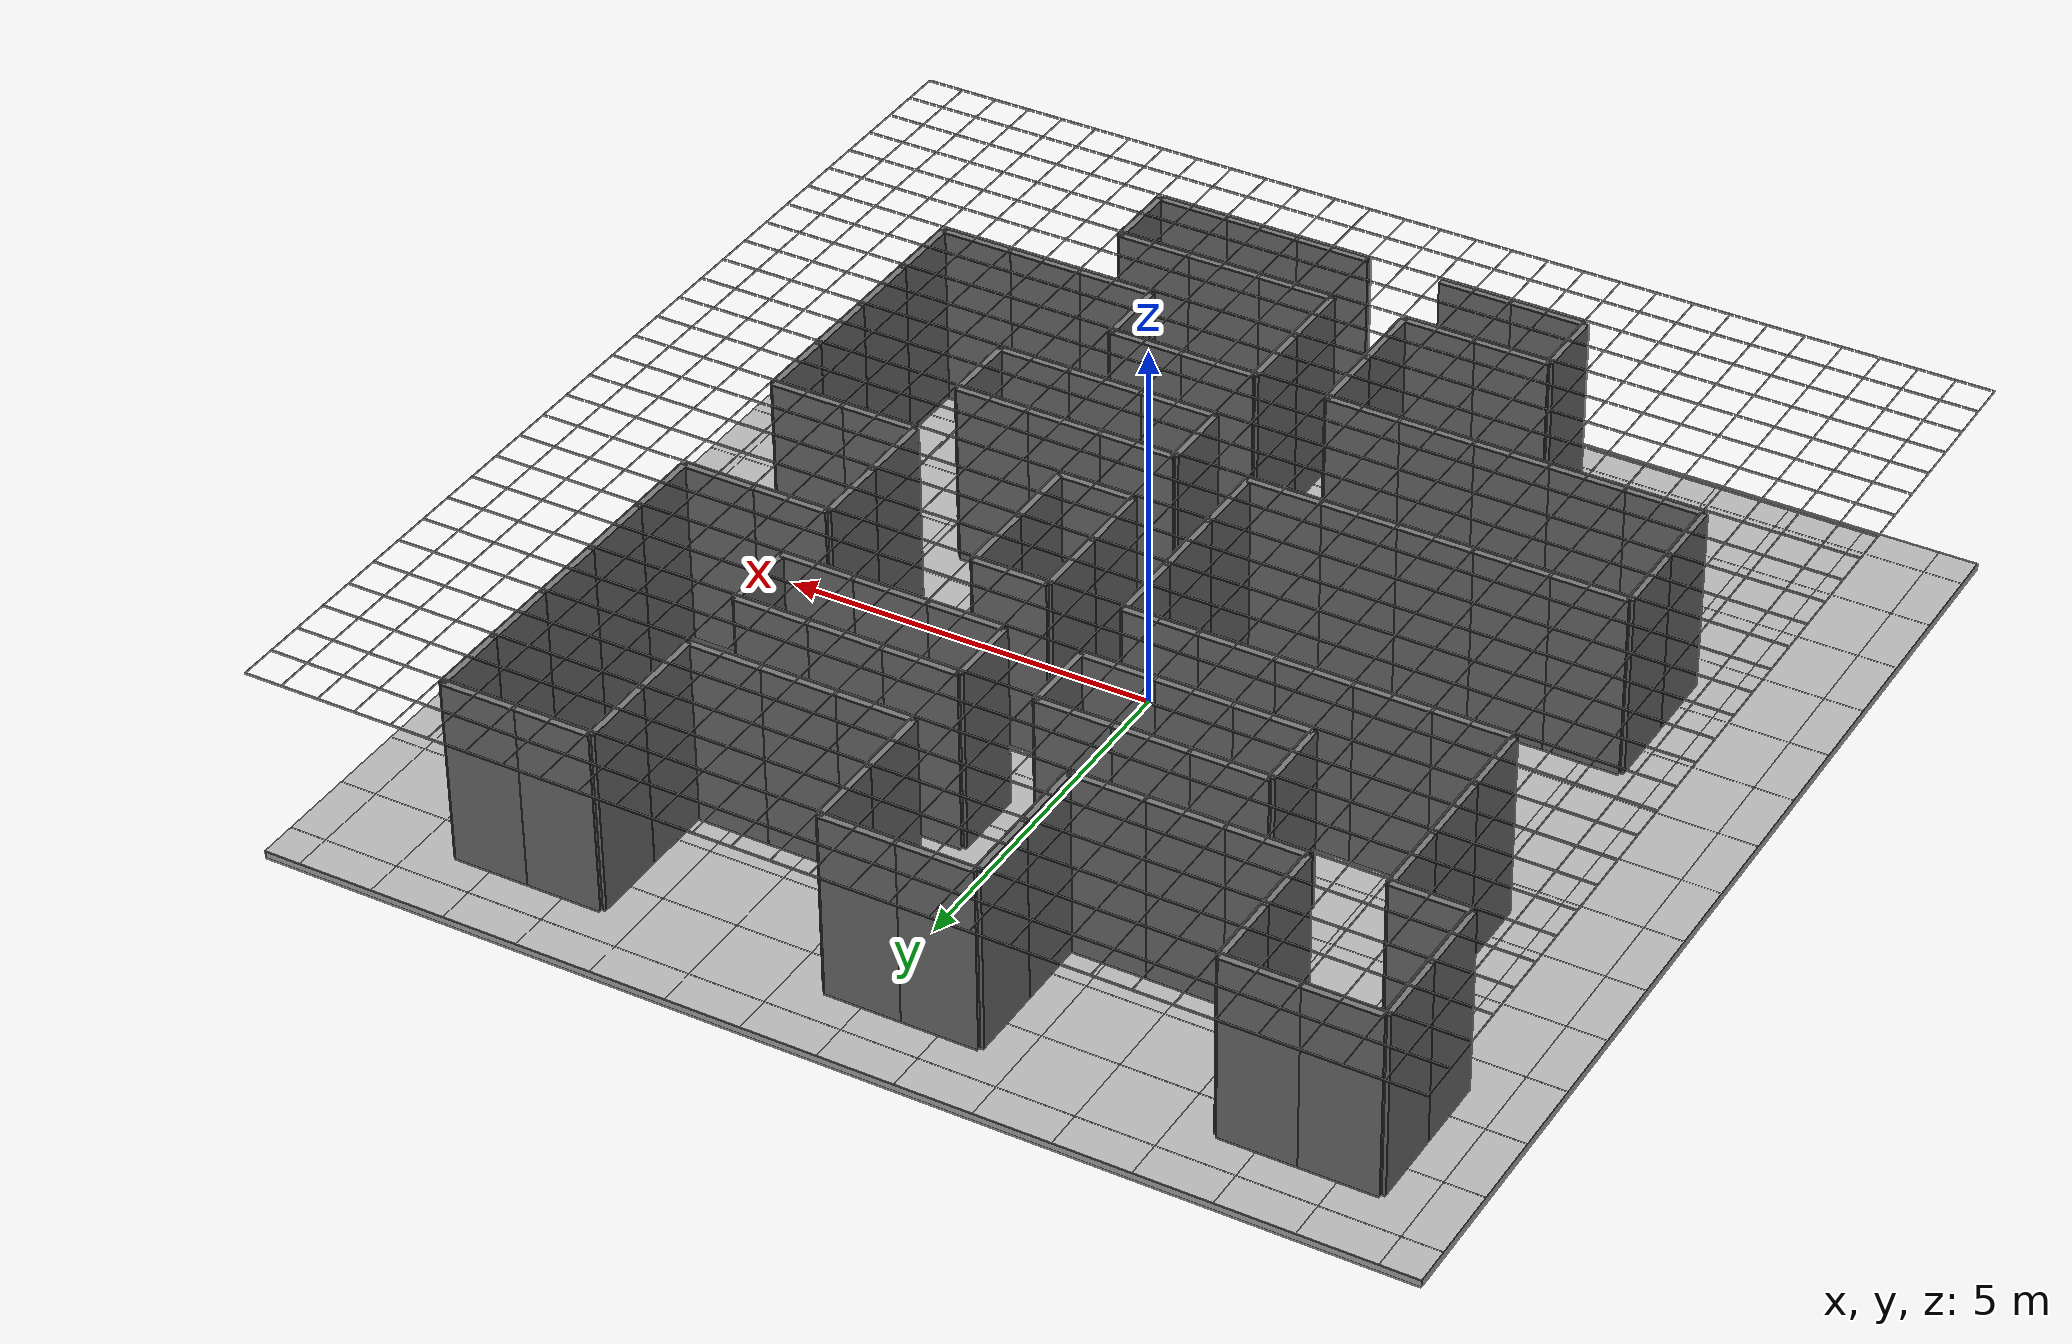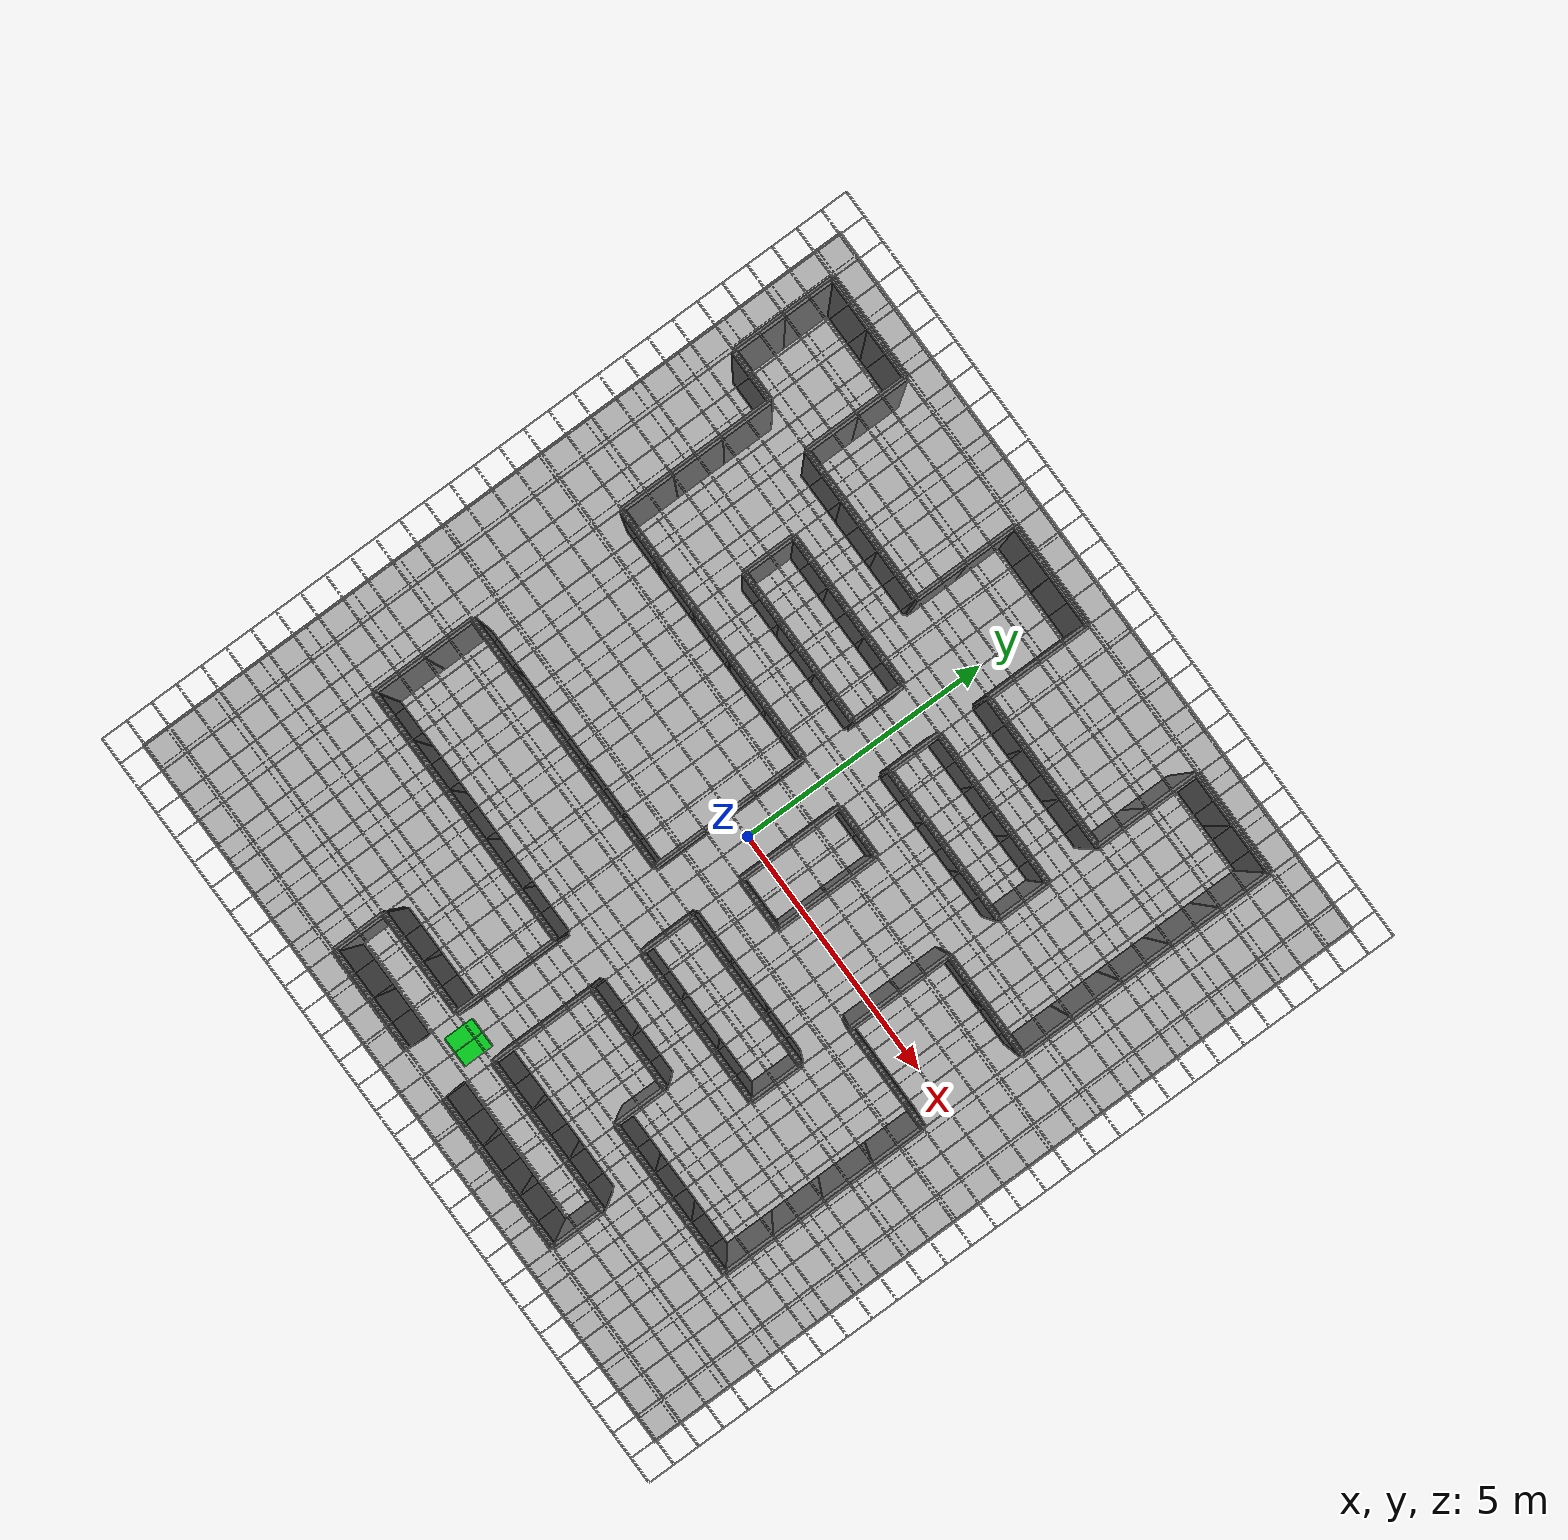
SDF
<?xml version="1.0"?>

<sdf version="1.9">

<world name="nidar_airmouse_building">

    <gravity>0 0 -9.81</gravity>

    <plugin
        filename="gz-sim-physics-system"
        name="gz::sim::systems::Physics"/>

    <plugin
        filename="gz-sim-user-commands-system"
        name="gz::sim::systems::UserCommands"/>

    <plugin
        filename="gz-sim-scene-broadcaster-system"
        name="gz::sim::systems::SceneBroadcaster"/>

    <light type="directional" name="sun">

        <pose>
            0 0 10 0 0 0
        </pose>

        <cast_shadows>true</cast_shadows>

        <direction>
            -0.3 0.2 -1.0
        </direction>

    </light>

    <model name="floor">

        <static>true</static>

        <pose>0 0 -0.05 0 0 0</pose>

        <link name="link">

            <collision name="collision">

                <geometry>

                    <box>
                        <size>
                            15 15 0.10
                        </size>
                    </box>

                </geometry>

            </collision>

            <visual name="visual">

                <geometry>

                    <box>
                        <size>
                            15 15 0.10
                        </size>
                    </box>

                </geometry>

                <material>

                    <ambient>
                        0.65 0.65 0.65 1
                    </ambient>

                    <diffuse>
                        0.70 0.70 0.70 1
                    </diffuse>

                </material>

            </visual>

        </link>

    </model>

        <model name="grid_x_0">

            <static>true</static>

            <pose>-7 0 0.006 0 0 0</pose>

            <link name="link">

                <visual name="visual">

                    <geometry>

                        <box>
                            <size>
                                0.008 15 0.002
                            </size>
                        </box>

                    </geometry>

                    <material>

                        <ambient>
                            0.25 0.25 0.25 0.35
                        </ambient>

                    </material>

                </visual>

            </link>

        </model>

        <model name="grid_x_1">

            <static>true</static>

            <pose>-6 0 0.006 0 0 0</pose>

            <link name="link">

                <visual name="visual">

                    <geometry>

                        <box>
                            <size>
                                0.008 15 0.002
                            </size>
                        </box>

                    </geometry>

                    <material>

                        <ambient>
                            0.25 0.25 0.25 0.35
                        </ambient>

                    </material>

                </visual>

            </link>

        </model>

        <model name="grid_x_2">

            <static>true</static>

            <pose>-5 0 0.006 0 0 0</pose>

            <link name="link">

                <visual name="visual">

                    <geometry>

                        <box>
                            <size>
                                0.008 15 0.002
                            </size>
                        </box>

                    </geometry>

                    <material>

                        <ambient>
                            0.25 0.25 0.25 0.35
                        </ambient>

                    </material>

                </visual>

            </link>

        </model>

        <model name="grid_x_3">

            <static>true</static>

            <pose>-4 0 0.006 0 0 0</pose>

            <link name="link">

                <visual name="visual">

                    <geometry>

                        <box>
                            <size>
                                0.008 15 0.002
                            </size>
                        </box>

                    </geometry>

                    <material>

                        <ambient>
                            0.25 0.25 0.25 0.35
                        </ambient>

                    </material>

                </visual>

            </link>

        </model>

        <model name="grid_x_4">

            <static>true</static>

            <pose>-3 0 0.006 0 0 0</pose>

            <link name="link">

                <visual name="visual">

                    <geometry>

                        <box>
                            <size>
                                0.008 15 0.002
                            </size>
                        </box>

                    </geometry>

                    <material>

                        <ambient>
                            0.25 0.25 0.25 0.35
                        </ambient>

                    </material>

                </visual>

            </link>

        </model>

        <model name="grid_x_5">

            <static>true</static>

            <pose>-2 0 0.006 0 0 0</pose>

            <link name="link">

                <visual name="visual">

                    <geometry>

                        <box>
                            <size>
                                0.008 15 0.002
                            </size>
                        </box>

                    </geometry>

                    <material>

                        <ambient>
                            0.25 0.25 0.25 0.35
                        </ambient>

                    </material>

                </visual>

            </link>

        </model>

        <model name="grid_x_6">

            <static>true</static>

            <pose>-1 0 0.006 0 0 0</pose>

            <link name="link">

                <visual name="visual">

                    <geometry>

                        <box>
                            <size>
                                0.008 15 0.002
                            </size>
                        </box>

                    </geometry>

                    <material>

                        <ambient>
                            0.25 0.25 0.25 0.35
                        </ambient>

                    </material>

                </visual>

            </link>

        </model>

        <model name="grid_x_7">

            <static>true</static>

            <pose>0 0 0.006 0 0 0</pose>

            <link name="link">

                <visual name="visual">

                    <geometry>

                        <box>
                            <size>
                                0.008 15 0.002
                            </size>
                        </box>

                    </geometry>

                    <material>

                        <ambient>
                            0.25 0.25 0.25 0.35
                        </ambient>

                    </material>

                </visual>

            </link>

        </model>

        <model name="grid_x_8">

            <static>true</static>

            <pose>1 0 0.006 0 0 0</pose>

            <link name="link">

                <visual name="visual">

                    <geometry>

                        <box>
                            <size>
                                0.008 15 0.002
                            </size>
                        </box>

                    </geometry>

                    <material>

                        <ambient>
                            0.25 0.25 0.25 0.35
                        </ambient>

                    </material>

                </visual>

            </link>

        </model>

        <model name="grid_x_9">

            <static>true</static>

            <pose>2 0 0.006 0 0 0</pose>

            <link name="link">

                <visual name="visual">

                    <geometry>

                        <box>
                            <size>
                                0.008 15 0.002
                            </size>
                        </box>

                    </geometry>

                    <material>

                        <ambient>
                            0.25 0.25 0.25 0.35
                        </ambient>

                    </material>

                </visual>

            </link>

        </model>

        <model name="grid_x_10">

            <static>true</static>

            <pose>3 0 0.006 0 0 0</pose>

            <link name="link">

                <visual name="visual">

                    <geometry>

                        <box>
                            <size>
                                0.008 15 0.002
                            </size>
                        </box>

                    </geometry>

                    <material>

                        <ambient>
                            0.25 0.25 0.25 0.35
                        </ambient>

                    </material>

                </visual>

            </link>

        </model>

        <model name="grid_x_11">

            <static>true</static>

            <pose>4 0 0.006 0 0 0</pose>

            <link name="link">

                <visual name="visual">

                    <geometry>

                        <box>
                            <size>
                                0.008 15 0.002
                            </size>
                        </box>

                    </geometry>

                    <material>

                        <ambient>
                            0.25 0.25 0.25 0.35
                        </ambient>

                    </material>

                </visual>

            </link>

        </model>

        <model name="grid_x_12">

            <static>true</static>

            <pose>5 0 0.006 0 0 0</pose>

            <link name="link">

                <visual name="visual">

                    <geometry>

                        <box>
                            <size>
                                0.008 15 0.002
                            </size>
                        </box>

                    </geometry>

                    <material>

                        <ambient>
                            0.25 0.25 0.25 0.35
                        </ambient>

                    </material>

                </visual>

            </link>

        </model>

        <model name="grid_x_13">

            <static>true</static>

            <pose>6 0 0.006 0 0 0</pose>

            <link name="link">

                <visual name="visual">

                    <geometry>

                        <box>
                            <size>
                                0.008 15 0.002
                            </size>
                        </box>

                    </geometry>

                    <material>

                        <ambient>
                            0.25 0.25 0.25 0.35
                        </ambient>

                    </material>

                </visual>

            </link>

        </model>

        <model name="grid_x_14">

            <static>true</static>

            <pose>7 0 0.006 0 0 0</pose>

            <link name="link">

                <visual name="visual">

                    <geometry>

                        <box>
                            <size>
                                0.008 15 0.002
                            </size>
                        </box>

                    </geometry>

                    <material>

                        <ambient>
                            0.25 0.25 0.25 0.35
                        </ambient>

                    </material>

                </visual>

            </link>

        </model>

        <model name="grid_y_15">

            <static>true</static>

            <pose>0 -7 0.007 0 0 0</pose>

            <link name="link">

                <visual name="visual">

                    <geometry>

                        <box>
                            <size>
                                15 0.008 0.002
                            </size>
                        </box>

                    </geometry>

                    <material>

                        <ambient>
                            0.25 0.25 0.25 0.35
                        </ambient>

                    </material>

                </visual>

            </link>

        </model>

        <model name="grid_y_16">

            <static>true</static>

            <pose>0 -6 0.007 0 0 0</pose>

            <link name="link">

                <visual name="visual">

                    <geometry>

                        <box>
                            <size>
                                15 0.008 0.002
                            </size>
                        </box>

                    </geometry>

                    <material>

                        <ambient>
                            0.25 0.25 0.25 0.35
                        </ambient>

                    </material>

                </visual>

            </link>

        </model>

        <model name="grid_y_17">

            <static>true</static>

            <pose>0 -5 0.007 0 0 0</pose>

            <link name="link">

                <visual name="visual">

                    <geometry>

                        <box>
                            <size>
                                15 0.008 0.002
                            </size>
                        </box>

                    </geometry>

                    <material>

                        <ambient>
                            0.25 0.25 0.25 0.35
                        </ambient>

                    </material>

                </visual>

            </link>

        </model>

        <model name="grid_y_18">

            <static>true</static>

            <pose>0 -4 0.007 0 0 0</pose>

            <link name="link">

                <visual name="visual">

                    <geometry>

                        <box>
                            <size>
                                15 0.008 0.002
                            </size>
                        </box>

                    </geometry>

                    <material>

                        <ambient>
                            0.25 0.25 0.25 0.35
                        </ambient>

                    </material>

                </visual>

            </link>

        </model>

        <model name="grid_y_19">

            <static>true</static>

            <pose>0 -3 0.007 0 0 0</pose>

            <link name="link">

                <visual name="visual">

                    <geometry>

                        <box>
                            <size>
                                15 0.008 0.002
                            </size>
                        </box>

                    </geometry>

                    <material>

                        <ambient>
                            0.25 0.25 0.25 0.35
                        </ambient>

                    </material>

                </visual>

            </link>

        </model>

        <model name="grid_y_20">

            <static>true</static>

            <pose>0 -2 0.007 0 0 0</pose>

            <link name="link">

                <visual name="visual">

                    <geometry>

                        <box>
                            <size>
                                15 0.008 0.002
                            </size>
                        </box>

                    </geometry>

                    <material>

                        <ambient>
                            0.25 0.25 0.25 0.35
                        </ambient>

                    </material>

                </visual>

            </link>

        </model>

        <model name="grid_y_21">

            <static>true</static>

            <pose>0 -1 0.007 0 0 0</pose>

            <link name="link">

                <visual name="visual">

                    <geometry>

                        <box>
                            <size>
                                15 0.008 0.002
                            </size>
                        </box>

                    </geometry>

                    <material>

                        <ambient>
                            0.25 0.25 0.25 0.35
                        </ambient>

                    </material>

                </visual>

            </link>

        </model>

        <model name="grid_y_22">

            <static>true</static>

            <pose>0 0 0.007 0 0 0</pose>

            <link name="link">

                <visual name="visual">

                    <geometry>

                        <box>
                            <size>
                                15 0.008 0.002
                            </size>
                        </box>

                    </geometry>

                    <material>

                        <ambient>
                            0.25 0.25 0.25 0.35
                        </ambient>

                    </material>

                </visual>

            </link>

        </model>

        <model name="grid_y_23">

            <static>true</static>

            <pose>0 1 0.007 0 0 0</pose>

            <link name="link">

                <visual name="visual">

                    <geometry>

                        <box>
                            <size>
                                15 0.008 0.002
                            </size>
                        </box>

                    </geometry>

                    <material>

                        <ambient>
                            0.25 0.25 0.25 0.35
                        </ambient>

                    </material>

                </visual>

            </link>

        </model>

        <model name="grid_y_24">

            <static>true</static>

            <pose>0 2 0.007 0 0 0</pose>

            <link name="link">

                <visual name="visual">

                    <geometry>

                        <box>
                            <size>
                                15 0.008 0.002
                            </size>
                        </box>

                    </geometry>

                    <material>

                        <ambient>
                            0.25 0.25 0.25 0.35
                        </ambient>

                    </material>

                </visual>

            </link>

        </model>

        <model name="grid_y_25">

            <static>true</static>

            <pose>0 3 0.007 0 0 0</pose>

            <link name="link">

                <visual name="visual">

                    <geometry>

                        <box>
                            <size>
                                15 0.008 0.002
                            </size>
                        </box>

                    </geometry>

                    <material>

                        <ambient>
                            0.25 0.25 0.25 0.35
                        </ambient>

                    </material>

                </visual>

            </link>

        </model>

        <model name="grid_y_26">

            <static>true</static>

            <pose>0 4 0.007 0 0 0</pose>

            <link name="link">

                <visual name="visual">

                    <geometry>

                        <box>
                            <size>
                                15 0.008 0.002
                            </size>
                        </box>

                    </geometry>

                    <material>

                        <ambient>
                            0.25 0.25 0.25 0.35
                        </ambient>

                    </material>

                </visual>

            </link>

        </model>

        <model name="grid_y_27">

            <static>true</static>

            <pose>0 5 0.007 0 0 0</pose>

            <link name="link">

                <visual name="visual">

                    <geometry>

                        <box>
                            <size>
                                15 0.008 0.002
                            </size>
                        </box>

                    </geometry>

                    <material>

                        <ambient>
                            0.25 0.25 0.25 0.35
                        </ambient>

                    </material>

                </visual>

            </link>

        </model>

        <model name="grid_y_28">

            <static>true</static>

            <pose>0 6 0.007 0 0 0</pose>

            <link name="link">

                <visual name="visual">

                    <geometry>

                        <box>
                            <size>
                                15 0.008 0.002
                            </size>
                        </box>

                    </geometry>

                    <material>

                        <ambient>
                            0.25 0.25 0.25 0.35
                        </ambient>

                    </material>

                </visual>

            </link>

        </model>

        <model name="grid_y_29">

            <static>true</static>

            <pose>0 7 0.007 0 0 0</pose>

            <link name="link">

                <visual name="visual">

                    <geometry>

                        <box>
                            <size>
                                15 0.008 0.002
                            </size>
                        </box>

                    </geometry>

                    <material>

                        <ambient>
                            0.25 0.25 0.25 0.35
                        </ambient>

                    </material>

                </visual>

            </link>

        </model>

    <model name="wall_0">

        <static>true</static>

        <pose>
            -6.0 6.5 1.25
            0 0 0
        </pose>

        <link name="link">

            <collision name="collision">

                <geometry>

                    <box>
                        <size>
                            1.0 0.1 2.5
                        </size>
                    </box>

                </geometry>

            </collision>

            <visual name="visual">

                <geometry>

                    <box>
                        <size>
                            1.0 0.1 2.5
                        </size>
                    </box>

                </geometry>

                <material>

                    <ambient>
                        0.35 0.35 0.35 1
                    </ambient>

                    <diffuse>
                        0.45 0.45 0.45 1
                    </diffuse>

                </material>

            </visual>

        </link>

    </model>

    <model name="wall_1">

        <static>true</static>

        <pose>
            -6.5 6.0 1.25
            0 0 0
        </pose>

        <link name="link">

            <collision name="collision">

                <geometry>

                    <box>
                        <size>
                            0.1 1.0 2.5
                        </size>
                    </box>

                </geometry>

            </collision>

            <visual name="visual">

                <geometry>

                    <box>
                        <size>
                            0.1 1.0 2.5
                        </size>
                    </box>

                </geometry>

                <material>

                    <ambient>
                        0.35 0.35 0.35 1
                    </ambient>

                    <diffuse>
                        0.45 0.45 0.45 1
                    </diffuse>

                </material>

            </visual>

        </link>

    </model>

    <model name="wall_2">

        <static>true</static>

        <pose>
            -5.0 6.5 1.25
            0 0 0
        </pose>

        <link name="link">

            <collision name="collision">

                <geometry>

                    <box>
                        <size>
                            1.0 0.1 2.5
                        </size>
                    </box>

                </geometry>

            </collision>

            <visual name="visual">

                <geometry>

                    <box>
                        <size>
                            1.0 0.1 2.5
                        </size>
                    </box>

                </geometry>

                <material>

                    <ambient>
                        0.35 0.35 0.35 1
                    </ambient>

                    <diffuse>
                        0.45 0.45 0.45 1
                    </diffuse>

                </material>

            </visual>

        </link>

    </model>

    <model name="wall_3">

        <static>true</static>

        <pose>
            -4.5 6.0 1.25
            0 0 0
        </pose>

        <link name="link">

            <collision name="collision">

                <geometry>

                    <box>
                        <size>
                            0.1 1.0 2.5
                        </size>
                    </box>

                </geometry>

            </collision>

            <visual name="visual">

                <geometry>

                    <box>
                        <size>
                            0.1 1.0 2.5
                        </size>
                    </box>

                </geometry>

                <material>

                    <ambient>
                        0.35 0.35 0.35 1
                    </ambient>

                    <diffuse>
                        0.45 0.45 0.45 1
                    </diffuse>

                </material>

            </visual>

        </link>

    </model>

    <model name="wall_4">

        <static>true</static>

        <pose>
            -1.0 6.5 1.25
            0 0 0
        </pose>

        <link name="link">

            <collision name="collision">

                <geometry>

                    <box>
                        <size>
                            1.0 0.1 2.5
                        </size>
                    </box>

                </geometry>

            </collision>

            <visual name="visual">

                <geometry>

                    <box>
                        <size>
                            1.0 0.1 2.5
                        </size>
                    </box>

                </geometry>

                <material>

                    <ambient>
                        0.35 0.35 0.35 1
                    </ambient>

                    <diffuse>
                        0.45 0.45 0.45 1
                    </diffuse>

                </material>

            </visual>

        </link>

    </model>

    <model name="wall_5">

        <static>true</static>

        <pose>
            -1.5 6.0 1.25
            0 0 0
        </pose>

        <link name="link">

            <collision name="collision">

                <geometry>

                    <box>
                        <size>
                            0.1 1.0 2.5
                        </size>
                    </box>

                </geometry>

            </collision>

            <visual name="visual">

                <geometry>

                    <box>
                        <size>
                            0.1 1.0 2.5
                        </size>
                    </box>

                </geometry>

                <material>

                    <ambient>
                        0.35 0.35 0.35 1
                    </ambient>

                    <diffuse>
                        0.45 0.45 0.45 1
                    </diffuse>

                </material>

            </visual>

        </link>

    </model>

    <model name="wall_6">

        <static>true</static>

        <pose>
            0.0 6.5 1.25
            0 0 0
        </pose>

        <link name="link">

            <collision name="collision">

                <geometry>

                    <box>
                        <size>
                            1.0 0.1 2.5
                        </size>
                    </box>

                </geometry>

            </collision>

            <visual name="visual">

                <geometry>

                    <box>
                        <size>
                            1.0 0.1 2.5
                        </size>
                    </box>

                </geometry>

                <material>

                    <ambient>
                        0.35 0.35 0.35 1
                    </ambient>

                    <diffuse>
                        0.45 0.45 0.45 1
                    </diffuse>

                </material>

            </visual>

        </link>

    </model>

    <model name="wall_7">

        <static>true</static>

        <pose>
            0.5 6.0 1.25
            0 0 0
        </pose>

        <link name="link">

            <collision name="collision">

                <geometry>

                    <box>
                        <size>
                            0.1 1.0 2.5
                        </size>
                    </box>

                </geometry>

            </collision>

            <visual name="visual">

                <geometry>

                    <box>
                        <size>
                            0.1 1.0 2.5
                        </size>
                    </box>

                </geometry>

                <material>

                    <ambient>
                        0.35 0.35 0.35 1
                    </ambient>

                    <diffuse>
                        0.45 0.45 0.45 1
                    </diffuse>

                </material>

            </visual>

        </link>

    </model>

    <model name="wall_8">

        <static>true</static>

        <pose>
            4.0 6.5 1.25
            0 0 0
        </pose>

        <link name="link">

            <collision name="collision">

                <geometry>

                    <box>
                        <size>
                            1.0 0.1 2.5
                        </size>
                    </box>

                </geometry>

            </collision>

            <visual name="visual">

                <geometry>

                    <box>
                        <size>
                            1.0 0.1 2.5
                        </size>
                    </box>

                </geometry>

                <material>

                    <ambient>
                        0.35 0.35 0.35 1
                    </ambient>

                    <diffuse>
                        0.45 0.45 0.45 1
                    </diffuse>

                </material>

            </visual>

        </link>

    </model>

    <model name="wall_9">

        <static>true</static>

        <pose>
            3.5 6.0 1.25
            0 0 0
        </pose>

        <link name="link">

            <collision name="collision">

                <geometry>

                    <box>
                        <size>
                            0.1 1.0 2.5
                        </size>
                    </box>

                </geometry>

            </collision>

            <visual name="visual">

                <geometry>

                    <box>
                        <size>
                            0.1 1.0 2.5
                        </size>
                    </box>

                </geometry>

                <material>

                    <ambient>
                        0.35 0.35 0.35 1
                    </ambient>

                    <diffuse>
                        0.45 0.45 0.45 1
                    </diffuse>

                </material>

            </visual>

        </link>

    </model>

    <model name="wall_10">

        <static>true</static>

        <pose>
            5.0 6.5 1.25
            0 0 0
        </pose>

        <link name="link">

            <collision name="collision">

                <geometry>

                    <box>
                        <size>
                            1.0 0.1 2.5
                        </size>
                    </box>

                </geometry>

            </collision>

            <visual name="visual">

                <geometry>

                    <box>
                        <size>
                            1.0 0.1 2.5
                        </size>
                    </box>

                </geometry>

                <material>

                    <ambient>
                        0.35 0.35 0.35 1
                    </ambient>

                    <diffuse>
                        0.45 0.45 0.45 1
                    </diffuse>

                </material>

            </visual>

        </link>

    </model>

    <model name="wall_11">

        <static>true</static>

        <pose>
            5.5 6.0 1.25
            0 0 0
        </pose>

        <link name="link">

            <collision name="collision">

                <geometry>

                    <box>
                        <size>
                            0.1 1.0 2.5
                        </size>
                    </box>

                </geometry>

            </collision>

            <visual name="visual">

                <geometry>

                    <box>
                        <size>
                            0.1 1.0 2.5
                        </size>
                    </box>

                </geometry>

                <material>

                    <ambient>
                        0.35 0.35 0.35 1
                    </ambient>

                    <diffuse>
                        0.45 0.45 0.45 1
                    </diffuse>

                </material>

            </visual>

        </link>

    </model>

    <model name="wall_12">

        <static>true</static>

        <pose>
            -6.0 4.5 1.25
            0 0 0
        </pose>

        <link name="link">

            <collision name="collision">

                <geometry>

                    <box>
                        <size>
                            1.0 0.1 2.5
                        </size>
                    </box>

                </geometry>

            </collision>

            <visual name="visual">

                <geometry>

                    <box>
                        <size>
                            1.0 0.1 2.5
                        </size>
                    </box>

                </geometry>

                <material>

                    <ambient>
                        0.35 0.35 0.35 1
                    </ambient>

                    <diffuse>
                        0.45 0.45 0.45 1
                    </diffuse>

                </material>

            </visual>

        </link>

    </model>

    <model name="wall_13">

        <static>true</static>

        <pose>
            -6.5 5.0 1.25
            0 0 0
        </pose>

        <link name="link">

            <collision name="collision">

                <geometry>

                    <box>
                        <size>
                            0.1 1.0 2.5
                        </size>
                    </box>

                </geometry>

            </collision>

            <visual name="visual">

                <geometry>

                    <box>
                        <size>
                            0.1 1.0 2.5
                        </size>
                    </box>

                </geometry>

                <material>

                    <ambient>
                        0.35 0.35 0.35 1
                    </ambient>

                    <diffuse>
                        0.45 0.45 0.45 1
                    </diffuse>

                </material>

            </visual>

        </link>

    </model>

    <model name="wall_14">

        <static>true</static>

        <pose>
            -4.5 5.0 1.25
            0 0 0
        </pose>

        <link name="link">

            <collision name="collision">

                <geometry>

                    <box>
                        <size>
                            0.1 1.0 2.5
                        </size>
                    </box>

                </geometry>

            </collision>

            <visual name="visual">

                <geometry>

                    <box>
                        <size>
                            0.1 1.0 2.5
                        </size>
                    </box>

                </geometry>

                <material>

                    <ambient>
                        0.35 0.35 0.35 1
                    </ambient>

                    <diffuse>
                        0.45 0.45 0.45 1
                    </diffuse>

                </material>

            </visual>

        </link>

    </model>

    <model name="wall_15">

        <static>true</static>

        <pose>
            -1.5 5.0 1.25
            0 0 0
        </pose>

        <link name="link">

            <collision name="collision">

                <geometry>

                    <box>
                        <size>
                            0.1 1.0 2.5
                        </size>
                    </box>

                </geometry>

            </collision>

            <visual name="visual">

                <geometry>

                    <box>
                        <size>
                            0.1 1.0 2.5
                        </size>
                    </box>

                </geometry>

                <material>

                    <ambient>
                        0.35 0.35 0.35 1
                    </ambient>

                    <diffuse>
                        0.45 0.45 0.45 1
                    </diffuse>

                </material>

            </visual>

        </link>

    </model>

    <model name="wall_16">

        <static>true</static>

        <pose>
            0.5 5.0 1.25
            0 0 0
        </pose>

        <link name="link">

            <collision name="collision">

                <geometry>

                    <box>
                        <size>
                            0.1 1.0 2.5
                        </size>
                    </box>

                </geometry>

            </collision>

            <visual name="visual">

                <geometry>

                    <box>
                        <size>
                            0.1 1.0 2.5
                        </size>
                    </box>

                </geometry>

                <material>

                    <ambient>
                        0.35 0.35 0.35 1
                    </ambient>

                    <diffuse>
                        0.45 0.45 0.45 1
                    </diffuse>

                </material>

            </visual>

        </link>

    </model>

    <model name="wall_17">

        <static>true</static>

        <pose>
            3.5 5.0 1.25
            0 0 0
        </pose>

        <link name="link">

            <collision name="collision">

                <geometry>

                    <box>
                        <size>
                            0.1 1.0 2.5
                        </size>
                    </box>

                </geometry>

            </collision>

            <visual name="visual">

                <geometry>

                    <box>
                        <size>
                            0.1 1.0 2.5
                        </size>
                    </box>

                </geometry>

                <material>

                    <ambient>
                        0.35 0.35 0.35 1
                    </ambient>

                    <diffuse>
                        0.45 0.45 0.45 1
                    </diffuse>

                </material>

            </visual>

        </link>

    </model>

    <model name="wall_18">

        <static>true</static>

        <pose>
            5.5 5.0 1.25
            0 0 0
        </pose>

        <link name="link">

            <collision name="collision">

                <geometry>

                    <box>
                        <size>
                            0.1 1.0 2.5
                        </size>
                    </box>

                </geometry>

            </collision>

            <visual name="visual">

                <geometry>

                    <box>
                        <size>
                            0.1 1.0 2.5
                        </size>
                    </box>

                </geometry>

                <material>

                    <ambient>
                        0.35 0.35 0.35 1
                    </ambient>

                    <diffuse>
                        0.45 0.45 0.45 1
                    </diffuse>

                </material>

            </visual>

        </link>

    </model>

    <model name="wall_19">

        <static>true</static>

        <pose>
            -5.5 4.0 1.25
            0 0 0
        </pose>

        <link name="link">

            <collision name="collision">

                <geometry>

                    <box>
                        <size>
                            0.1 1.0 2.5
                        </size>
                    </box>

                </geometry>

            </collision>

            <visual name="visual">

                <geometry>

                    <box>
                        <size>
                            0.1 1.0 2.5
                        </size>
                    </box>

                </geometry>

                <material>

                    <ambient>
                        0.35 0.35 0.35 1
                    </ambient>

                    <diffuse>
                        0.45 0.45 0.45 1
                    </diffuse>

                </material>

            </visual>

        </link>

    </model>

    <model name="wall_20">

        <static>true</static>

        <pose>
            -4.0 4.5 1.25
            0 0 0
        </pose>

        <link name="link">

            <collision name="collision">

                <geometry>

                    <box>
                        <size>
                            1.0 0.1 2.5
                        </size>
                    </box>

                </geometry>

            </collision>

            <visual name="visual">

                <geometry>

                    <box>
                        <size>
                            1.0 0.1 2.5
                        </size>
                    </box>

                </geometry>

                <material>

                    <ambient>
                        0.35 0.35 0.35 1
                    </ambient>

                    <diffuse>
                        0.45 0.45 0.45 1
                    </diffuse>

                </material>

            </visual>

        </link>

    </model>

    <model name="wall_21">

        <static>true</static>

        <pose>
            -3.0 4.5 1.25
            0 0 0
        </pose>

        <link name="link">

            <collision name="collision">

                <geometry>

                    <box>
                        <size>
                            1.0 0.1 2.5
                        </size>
                    </box>

                </geometry>

            </collision>

            <visual name="visual">

                <geometry>

                    <box>
                        <size>
                            1.0 0.1 2.5
                        </size>
                    </box>

                </geometry>

                <material>

                    <ambient>
                        0.35 0.35 0.35 1
                    </ambient>

                    <diffuse>
                        0.45 0.45 0.45 1
                    </diffuse>

                </material>

            </visual>

        </link>

    </model>

    <model name="wall_22">

        <static>true</static>

        <pose>
            -3.0 3.5 1.25
            0 0 0
        </pose>

        <link name="link">

            <collision name="collision">

                <geometry>

                    <box>
                        <size>
                            1.0 0.1 2.5
                        </size>
                    </box>

                </geometry>

            </collision>

            <visual name="visual">

                <geometry>

                    <box>
                        <size>
                            1.0 0.1 2.5
                        </size>
                    </box>

                </geometry>

                <material>

                    <ambient>
                        0.35 0.35 0.35 1
                    </ambient>

                    <diffuse>
                        0.45 0.45 0.45 1
                    </diffuse>

                </material>

            </visual>

        </link>

    </model>

    <model name="wall_23">

        <static>true</static>

        <pose>
            -2.0 4.5 1.25
            0 0 0
        </pose>

        <link name="link">

            <collision name="collision">

                <geometry>

                    <box>
                        <size>
                            1.0 0.1 2.5
                        </size>
                    </box>

                </geometry>

            </collision>

            <visual name="visual">

                <geometry>

                    <box>
                        <size>
                            1.0 0.1 2.5
                        </size>
                    </box>

                </geometry>

                <material>

                    <ambient>
                        0.35 0.35 0.35 1
                    </ambient>

                    <diffuse>
                        0.45 0.45 0.45 1
                    </diffuse>

                </material>

            </visual>

        </link>

    </model>

    <model name="wall_24">

        <static>true</static>

        <pose>
            -2.0 3.5 1.25
            0 0 0
        </pose>

        <link name="link">

            <collision name="collision">

                <geometry>

                    <box>
                        <size>
                            1.0 0.1 2.5
                        </size>
                    </box>

                </geometry>

            </collision>

            <visual name="visual">

                <geometry>

                    <box>
                        <size>
                            1.0 0.1 2.5
                        </size>
                    </box>

                </geometry>

                <material>

                    <ambient>
                        0.35 0.35 0.35 1
                    </ambient>

                    <diffuse>
                        0.45 0.45 0.45 1
                    </diffuse>

                </material>

            </visual>

        </link>

    </model>

    <model name="wall_25">

        <static>true</static>

        <pose>
            -1.0 3.5 1.25
            0 0 0
        </pose>

        <link name="link">

            <collision name="collision">

                <geometry>

                    <box>
                        <size>
                            1.0 0.1 2.5
                        </size>
                    </box>

                </geometry>

            </collision>

            <visual name="visual">

                <geometry>

                    <box>
                        <size>
                            1.0 0.1 2.5
                        </size>
                    </box>

                </geometry>

                <material>

                    <ambient>
                        0.35 0.35 0.35 1
                    </ambient>

                    <diffuse>
                        0.45 0.45 0.45 1
                    </diffuse>

                </material>

            </visual>

        </link>

    </model>

    <model name="wall_26">

        <static>true</static>

        <pose>
            1.0 4.5 1.25
            0 0 0
        </pose>

        <link name="link">

            <collision name="collision">

                <geometry>

                    <box>
                        <size>
                            1.0 0.1 2.5
                        </size>
                    </box>

                </geometry>

            </collision>

            <visual name="visual">

                <geometry>

                    <box>
                        <size>
                            1.0 0.1 2.5
                        </size>
                    </box>

                </geometry>

                <material>

                    <ambient>
                        0.35 0.35 0.35 1
                    </ambient>

                    <diffuse>
                        0.45 0.45 0.45 1
                    </diffuse>

                </material>

            </visual>

        </link>

    </model>

    <model name="wall_27">

        <static>true</static>

        <pose>
            1.0 3.5 1.25
            0 0 0
        </pose>

        <link name="link">

            <collision name="collision">

                <geometry>

                    <box>
                        <size>
                            1.0 0.1 2.5
                        </size>
                    </box>

                </geometry>

            </collision>

            <visual name="visual">

                <geometry>

                    <box>
                        <size>
                            1.0 0.1 2.5
                        </size>
                    </box>

                </geometry>

                <material>

                    <ambient>
                        0.35 0.35 0.35 1
                    </ambient>

                    <diffuse>
                        0.45 0.45 0.45 1
                    </diffuse>

                </material>

            </visual>

        </link>

    </model>

    <model name="wall_28">

        <static>true</static>

        <pose>
            2.0 4.5 1.25
            0 0 0
        </pose>

        <link name="link">

            <collision name="collision">

                <geometry>

                    <box>
                        <size>
                            1.0 0.1 2.5
                        </size>
                    </box>

                </geometry>

            </collision>

            <visual name="visual">

                <geometry>

                    <box>
                        <size>
                            1.0 0.1 2.5
                        </size>
                    </box>

                </geometry>

                <material>

                    <ambient>
                        0.35 0.35 0.35 1
                    </ambient>

                    <diffuse>
                        0.45 0.45 0.45 1
                    </diffuse>

                </material>

            </visual>

        </link>

    </model>

    <model name="wall_29">

        <static>true</static>

        <pose>
            2.0 3.5 1.25
            0 0 0
        </pose>

        <link name="link">

            <collision name="collision">

                <geometry>

                    <box>
                        <size>
                            1.0 0.1 2.5
                        </size>
                    </box>

                </geometry>

            </collision>

            <visual name="visual">

                <geometry>

                    <box>
                        <size>
                            1.0 0.1 2.5
                        </size>
                    </box>

                </geometry>

                <material>

                    <ambient>
                        0.35 0.35 0.35 1
                    </ambient>

                    <diffuse>
                        0.45 0.45 0.45 1
                    </diffuse>

                </material>

            </visual>

        </link>

    </model>

    <model name="wall_30">

        <static>true</static>

        <pose>
            3.0 4.5 1.25
            0 0 0
        </pose>

        <link name="link">

            <collision name="collision">

                <geometry>

                    <box>
                        <size>
                            1.0 0.1 2.5
                        </size>
                    </box>

                </geometry>

            </collision>

            <visual name="visual">

                <geometry>

                    <box>
                        <size>
                            1.0 0.1 2.5
                        </size>
                    </box>

                </geometry>

                <material>

                    <ambient>
                        0.35 0.35 0.35 1
                    </ambient>

                    <diffuse>
                        0.45 0.45 0.45 1
                    </diffuse>

                </material>

            </visual>

        </link>

    </model>

    <model name="wall_31">

        <static>true</static>

        <pose>
            3.0 3.5 1.25
            0 0 0
        </pose>

        <link name="link">

            <collision name="collision">

                <geometry>

                    <box>
                        <size>
                            1.0 0.1 2.5
                        </size>
                    </box>

                </geometry>

            </collision>

            <visual name="visual">

                <geometry>

                    <box>
                        <size>
                            1.0 0.1 2.5
                        </size>
                    </box>

                </geometry>

                <material>

                    <ambient>
                        0.35 0.35 0.35 1
                    </ambient>

                    <diffuse>
                        0.45 0.45 0.45 1
                    </diffuse>

                </material>

            </visual>

        </link>

    </model>

    <model name="wall_32">

        <static>true</static>

        <pose>
            5.5 4.0 1.25
            0 0 0
        </pose>

        <link name="link">

            <collision name="collision">

                <geometry>

                    <box>
                        <size>
                            0.1 1.0 2.5
                        </size>
                    </box>

                </geometry>

            </collision>

            <visual name="visual">

                <geometry>

                    <box>
                        <size>
                            0.1 1.0 2.5
                        </size>
                    </box>

                </geometry>

                <material>

                    <ambient>
                        0.35 0.35 0.35 1
                    </ambient>

                    <diffuse>
                        0.45 0.45 0.45 1
                    </diffuse>

                </material>

            </visual>

        </link>

    </model>

    <model name="wall_33">

        <static>true</static>

        <pose>
            -5.5 3.0 1.25
            0 0 0
        </pose>

        <link name="link">

            <collision name="collision">

                <geometry>

                    <box>
                        <size>
                            0.1 1.0 2.5
                        </size>
                    </box>

                </geometry>

            </collision>

            <visual name="visual">

                <geometry>

                    <box>
                        <size>
                            0.1 1.0 2.5
                        </size>
                    </box>

                </geometry>

                <material>

                    <ambient>
                        0.35 0.35 0.35 1
                    </ambient>

                    <diffuse>
                        0.45 0.45 0.45 1
                    </diffuse>

                </material>

            </visual>

        </link>

    </model>

    <model name="wall_34">

        <static>true</static>

        <pose>
            -3.5 3.0 1.25
            0 0 0
        </pose>

        <link name="link">

            <collision name="collision">

                <geometry>

                    <box>
                        <size>
                            0.1 1.0 2.5
                        </size>
                    </box>

                </geometry>

            </collision>

            <visual name="visual">

                <geometry>

                    <box>
                        <size>
                            0.1 1.0 2.5
                        </size>
                    </box>

                </geometry>

                <material>

                    <ambient>
                        0.35 0.35 0.35 1
                    </ambient>

                    <diffuse>
                        0.45 0.45 0.45 1
                    </diffuse>

                </material>

            </visual>

        </link>

    </model>

    <model name="wall_35">

        <static>true</static>

        <pose>
            -0.5 3.0 1.25
            0 0 0
        </pose>

        <link name="link">

            <collision name="collision">

                <geometry>

                    <box>
                        <size>
                            0.1 1.0 2.5
                        </size>
                    </box>

                </geometry>

            </collision>

            <visual name="visual">

                <geometry>

                    <box>
                        <size>
                            0.1 1.0 2.5
                        </size>
                    </box>

                </geometry>

                <material>

                    <ambient>
                        0.35 0.35 0.35 1
                    </ambient>

                    <diffuse>
                        0.45 0.45 0.45 1
                    </diffuse>

                </material>

            </visual>

        </link>

    </model>

    <model name="wall_36">

        <static>true</static>

        <pose>
            0.5 3.0 1.25
            0 0 0
        </pose>

        <link name="link">

            <collision name="collision">

                <geometry>

                    <box>
                        <size>
                            0.1 1.0 2.5
                        </size>
                    </box>

                </geometry>

            </collision>

            <visual name="visual">

                <geometry>

                    <box>
                        <size>
                            0.1 1.0 2.5
                        </size>
                    </box>

                </geometry>

                <material>

                    <ambient>
                        0.35 0.35 0.35 1
                    </ambient>

                    <diffuse>
                        0.45 0.45 0.45 1
                    </diffuse>

                </material>

            </visual>

        </link>

    </model>

    <model name="wall_37">

        <static>true</static>

        <pose>
            3.5 3.0 1.25
            0 0 0
        </pose>

        <link name="link">

            <collision name="collision">

                <geometry>

                    <box>
                        <size>
                            0.1 1.0 2.5
                        </size>
                    </box>

                </geometry>

            </collision>

            <visual name="visual">

                <geometry>

                    <box>
                        <size>
                            0.1 1.0 2.5
                        </size>
                    </box>

                </geometry>

                <material>

                    <ambient>
                        0.35 0.35 0.35 1
                    </ambient>

                    <diffuse>
                        0.45 0.45 0.45 1
                    </diffuse>

                </material>

            </visual>

        </link>

    </model>

    <model name="wall_38">

        <static>true</static>

        <pose>
            5.5 3.0 1.25
            0 0 0
        </pose>

        <link name="link">

            <collision name="collision">

                <geometry>

                    <box>
                        <size>
                            0.1 1.0 2.5
                        </size>
                    </box>

                </geometry>

            </collision>

            <visual name="visual">

                <geometry>

                    <box>
                        <size>
                            0.1 1.0 2.5
                        </size>
                    </box>

                </geometry>

                <material>

                    <ambient>
                        0.35 0.35 0.35 1
                    </ambient>

                    <diffuse>
                        0.45 0.45 0.45 1
                    </diffuse>

                </material>

            </visual>

        </link>

    </model>

    <model name="wall_39">

        <static>true</static>

        <pose>
            -5.0 1.5 1.25
            0 0 0
        </pose>

        <link name="link">

            <collision name="collision">

                <geometry>

                    <box>
                        <size>
                            1.0 0.1 2.5
                        </size>
                    </box>

                </geometry>

            </collision>

            <visual name="visual">

                <geometry>

                    <box>
                        <size>
                            1.0 0.1 2.5
                        </size>
                    </box>

                </geometry>

                <material>

                    <ambient>
                        0.35 0.35 0.35 1
                    </ambient>

                    <diffuse>
                        0.45 0.45 0.45 1
                    </diffuse>

                </material>

            </visual>

        </link>

    </model>

    <model name="wall_40">

        <static>true</static>

        <pose>
            -5.5 2.0 1.25
            0 0 0
        </pose>

        <link name="link">

            <collision name="collision">

                <geometry>

                    <box>
                        <size>
                            0.1 1.0 2.5
                        </size>
                    </box>

                </geometry>

            </collision>

            <visual name="visual">

                <geometry>

                    <box>
                        <size>
                            0.1 1.0 2.5
                        </size>
                    </box>

                </geometry>

                <material>

                    <ambient>
                        0.35 0.35 0.35 1
                    </ambient>

                    <diffuse>
                        0.45 0.45 0.45 1
                    </diffuse>

                </material>

            </visual>

        </link>

    </model>

    <model name="wall_41">

        <static>true</static>

        <pose>
            -4.0 1.5 1.25
            0 0 0
        </pose>

        <link name="link">

            <collision name="collision">

                <geometry>

                    <box>
                        <size>
                            1.0 0.1 2.5
                        </size>
                    </box>

                </geometry>

            </collision>

            <visual name="visual">

                <geometry>

                    <box>
                        <size>
                            1.0 0.1 2.5
                        </size>
                    </box>

                </geometry>

                <material>

                    <ambient>
                        0.35 0.35 0.35 1
                    </ambient>

                    <diffuse>
                        0.45 0.45 0.45 1
                    </diffuse>

                </material>

            </visual>

        </link>

    </model>

    <model name="wall_42">

        <static>true</static>

        <pose>
            -3.0 2.5 1.25
            0 0 0
        </pose>

        <link name="link">

            <collision name="collision">

                <geometry>

                    <box>
                        <size>
                            1.0 0.1 2.5
                        </size>
                    </box>

                </geometry>

            </collision>

            <visual name="visual">

                <geometry>

                    <box>
                        <size>
                            1.0 0.1 2.5
                        </size>
                    </box>

                </geometry>

                <material>

                    <ambient>
                        0.35 0.35 0.35 1
                    </ambient>

                    <diffuse>
                        0.45 0.45 0.45 1
                    </diffuse>

                </material>

            </visual>

        </link>

    </model>

    <model name="wall_43">

        <static>true</static>

        <pose>
            -3.0 1.5 1.25
            0 0 0
        </pose>

        <link name="link">

            <collision name="collision">

                <geometry>

                    <box>
                        <size>
                            1.0 0.1 2.5
                        </size>
                    </box>

                </geometry>

            </collision>

            <visual name="visual">

                <geometry>

                    <box>
                        <size>
                            1.0 0.1 2.5
                        </size>
                    </box>

                </geometry>

                <material>

                    <ambient>
                        0.35 0.35 0.35 1
                    </ambient>

                    <diffuse>
                        0.45 0.45 0.45 1
                    </diffuse>

                </material>

            </visual>

        </link>

    </model>

    <model name="wall_44">

        <static>true</static>

        <pose>
            -2.0 2.5 1.25
            0 0 0
        </pose>

        <link name="link">

            <collision name="collision">

                <geometry>

                    <box>
                        <size>
                            1.0 0.1 2.5
                        </size>
                    </box>

                </geometry>

            </collision>

            <visual name="visual">

                <geometry>

                    <box>
                        <size>
                            1.0 0.1 2.5
                        </size>
                    </box>

                </geometry>

                <material>

                    <ambient>
                        0.35 0.35 0.35 1
                    </ambient>

                    <diffuse>
                        0.45 0.45 0.45 1
                    </diffuse>

                </material>

            </visual>

        </link>

    </model>

    <model name="wall_45">

        <static>true</static>

        <pose>
            -2.0 1.5 1.25
            0 0 0
        </pose>

        <link name="link">

            <collision name="collision">

                <geometry>

                    <box>
                        <size>
                            1.0 0.1 2.5
                        </size>
                    </box>

                </geometry>

            </collision>

            <visual name="visual">

                <geometry>

                    <box>
                        <size>
                            1.0 0.1 2.5
                        </size>
                    </box>

                </geometry>

                <material>

                    <ambient>
                        0.35 0.35 0.35 1
                    </ambient>

                    <diffuse>
                        0.45 0.45 0.45 1
                    </diffuse>

                </material>

            </visual>

        </link>

    </model>

    <model name="wall_46">

        <static>true</static>

        <pose>
            -1.0 2.5 1.25
            0 0 0
        </pose>

        <link name="link">

            <collision name="collision">

                <geometry>

                    <box>
                        <size>
                            1.0 0.1 2.5
                        </size>
                    </box>

                </geometry>

            </collision>

            <visual name="visual">

                <geometry>

                    <box>
                        <size>
                            1.0 0.1 2.5
                        </size>
                    </box>

                </geometry>

                <material>

                    <ambient>
                        0.35 0.35 0.35 1
                    </ambient>

                    <diffuse>
                        0.45 0.45 0.45 1
                    </diffuse>

                </material>

            </visual>

        </link>

    </model>

    <model name="wall_47">

        <static>true</static>

        <pose>
            -1.0 1.5 1.25
            0 0 0
        </pose>

        <link name="link">

            <collision name="collision">

                <geometry>

                    <box>
                        <size>
                            1.0 0.1 2.5
                        </size>
                    </box>

                </geometry>

            </collision>

            <visual name="visual">

                <geometry>

                    <box>
                        <size>
                            1.0 0.1 2.5
                        </size>
                    </box>

                </geometry>

                <material>

                    <ambient>
                        0.35 0.35 0.35 1
                    </ambient>

                    <diffuse>
                        0.45 0.45 0.45 1
                    </diffuse>

                </material>

            </visual>

        </link>

    </model>

    <model name="wall_48">

        <static>true</static>

        <pose>
            1.0 2.5 1.25
            0 0 0
        </pose>

        <link name="link">

            <collision name="collision">

                <geometry>

                    <box>
                        <size>
                            1.0 0.1 2.5
                        </size>
                    </box>

                </geometry>

            </collision>

            <visual name="visual">

                <geometry>

                    <box>
                        <size>
                            1.0 0.1 2.5
                        </size>
                    </box>

                </geometry>

                <material>

                    <ambient>
                        0.35 0.35 0.35 1
                    </ambient>

                    <diffuse>
                        0.45 0.45 0.45 1
                    </diffuse>

                </material>

            </visual>

        </link>

    </model>

    <model name="wall_49">

        <static>true</static>

        <pose>
            1.0 1.5 1.25
            0 0 0
        </pose>

        <link name="link">

            <collision name="collision">

                <geometry>

                    <box>
                        <size>
                            1.0 0.1 2.5
                        </size>
                    </box>

                </geometry>

            </collision>

            <visual name="visual">

                <geometry>

                    <box>
                        <size>
                            1.0 0.1 2.5
                        </size>
                    </box>

                </geometry>

                <material>

                    <ambient>
                        0.35 0.35 0.35 1
                    </ambient>

                    <diffuse>
                        0.45 0.45 0.45 1
                    </diffuse>

                </material>

            </visual>

        </link>

    </model>

    <model name="wall_50">

        <static>true</static>

        <pose>
            2.0 2.5 1.25
            0 0 0
        </pose>

        <link name="link">

            <collision name="collision">

                <geometry>

                    <box>
                        <size>
                            1.0 0.1 2.5
                        </size>
                    </box>

                </geometry>

            </collision>

            <visual name="visual">

                <geometry>

                    <box>
                        <size>
                            1.0 0.1 2.5
                        </size>
                    </box>

                </geometry>

                <material>

                    <ambient>
                        0.35 0.35 0.35 1
                    </ambient>

                    <diffuse>
                        0.45 0.45 0.45 1
                    </diffuse>

                </material>

            </visual>

        </link>

    </model>

    <model name="wall_51">

        <static>true</static>

        <pose>
            3.0 2.5 1.25
            0 0 0
        </pose>

        <link name="link">

            <collision name="collision">

                <geometry>

                    <box>
                        <size>
                            1.0 0.1 2.5
                        </size>
                    </box>

                </geometry>

            </collision>

            <visual name="visual">

                <geometry>

                    <box>
                        <size>
                            1.0 0.1 2.5
                        </size>
                    </box>

                </geometry>

                <material>

                    <ambient>
                        0.35 0.35 0.35 1
                    </ambient>

                    <diffuse>
                        0.45 0.45 0.45 1
                    </diffuse>

                </material>

            </visual>

        </link>

    </model>

    <model name="wall_52">

        <static>true</static>

        <pose>
            4.0 1.5 1.25
            0 0 0
        </pose>

        <link name="link">

            <collision name="collision">

                <geometry>

                    <box>
                        <size>
                            1.0 0.1 2.5
                        </size>
                    </box>

                </geometry>

            </collision>

            <visual name="visual">

                <geometry>

                    <box>
                        <size>
                            1.0 0.1 2.5
                        </size>
                    </box>

                </geometry>

                <material>

                    <ambient>
                        0.35 0.35 0.35 1
                    </ambient>

                    <diffuse>
                        0.45 0.45 0.45 1
                    </diffuse>

                </material>

            </visual>

        </link>

    </model>

    <model name="wall_53">

        <static>true</static>

        <pose>
            5.0 1.5 1.25
            0 0 0
        </pose>

        <link name="link">

            <collision name="collision">

                <geometry>

                    <box>
                        <size>
                            1.0 0.1 2.5
                        </size>
                    </box>

                </geometry>

            </collision>

            <visual name="visual">

                <geometry>

                    <box>
                        <size>
                            1.0 0.1 2.5
                        </size>
                    </box>

                </geometry>

                <material>

                    <ambient>
                        0.35 0.35 0.35 1
                    </ambient>

                    <diffuse>
                        0.45 0.45 0.45 1
                    </diffuse>

                </material>

            </visual>

        </link>

    </model>

    <model name="wall_54">

        <static>true</static>

        <pose>
            5.5 2.0 1.25
            0 0 0
        </pose>

        <link name="link">

            <collision name="collision">

                <geometry>

                    <box>
                        <size>
                            0.1 1.0 2.5
                        </size>
                    </box>

                </geometry>

            </collision>

            <visual name="visual">

                <geometry>

                    <box>
                        <size>
                            0.1 1.0 2.5
                        </size>
                    </box>

                </geometry>

                <material>

                    <ambient>
                        0.35 0.35 0.35 1
                    </ambient>

                    <diffuse>
                        0.45 0.45 0.45 1
                    </diffuse>

                </material>

            </visual>

        </link>

    </model>

    <model name="wall_55">

        <static>true</static>

        <pose>
            -0.5 1.0 1.25
            0 0 0
        </pose>

        <link name="link">

            <collision name="collision">

                <geometry>

                    <box>
                        <size>
                            0.1 1.0 2.5
                        </size>
                    </box>

                </geometry>

            </collision>

            <visual name="visual">

                <geometry>

                    <box>
                        <size>
                            0.1 1.0 2.5
                        </size>
                    </box>

                </geometry>

                <material>

                    <ambient>
                        0.35 0.35 0.35 1
                    </ambient>

                    <diffuse>
                        0.45 0.45 0.45 1
                    </diffuse>

                </material>

            </visual>

        </link>

    </model>

    <model name="wall_56">

        <static>true</static>

        <pose>
            0.5 1.0 1.25
            0 0 0
        </pose>

        <link name="link">

            <collision name="collision">

                <geometry>

                    <box>
                        <size>
                            0.1 1.0 2.5
                        </size>
                    </box>

                </geometry>

            </collision>

            <visual name="visual">

                <geometry>

                    <box>
                        <size>
                            0.1 1.0 2.5
                        </size>
                    </box>

                </geometry>

                <material>

                    <ambient>
                        0.35 0.35 0.35 1
                    </ambient>

                    <diffuse>
                        0.45 0.45 0.45 1
                    </diffuse>

                </material>

            </visual>

        </link>

    </model>

    <model name="wall_57">

        <static>true</static>

        <pose>
            1.5 1.0 1.25
            0 0 0
        </pose>

        <link name="link">

            <collision name="collision">

                <geometry>

                    <box>
                        <size>
                            0.1 1.0 2.5
                        </size>
                    </box>

                </geometry>

            </collision>

            <visual name="visual">

                <geometry>

                    <box>
                        <size>
                            0.1 1.0 2.5
                        </size>
                    </box>

                </geometry>

                <material>

                    <ambient>
                        0.35 0.35 0.35 1
                    </ambient>

                    <diffuse>
                        0.45 0.45 0.45 1
                    </diffuse>

                </material>

            </visual>

        </link>

    </model>

    <model name="wall_58">

        <static>true</static>

        <pose>
            3.5 1.0 1.25
            0 0 0
        </pose>

        <link name="link">

            <collision name="collision">

                <geometry>

                    <box>
                        <size>
                            0.1 1.0 2.5
                        </size>
                    </box>

                </geometry>

            </collision>

            <visual name="visual">

                <geometry>

                    <box>
                        <size>
                            0.1 1.0 2.5
                        </size>
                    </box>

                </geometry>

                <material>

                    <ambient>
                        0.35 0.35 0.35 1
                    </ambient>

                    <diffuse>
                        0.45 0.45 0.45 1
                    </diffuse>

                </material>

            </visual>

        </link>

    </model>

    <model name="wall_59">

        <static>true</static>

        <pose>
            -0.5 0.0 1.25
            0 0 0
        </pose>

        <link name="link">

            <collision name="collision">

                <geometry>

                    <box>
                        <size>
                            0.1 1.0 2.5
                        </size>
                    </box>

                </geometry>

            </collision>

            <visual name="visual">

                <geometry>

                    <box>
                        <size>
                            0.1 1.0 2.5
                        </size>
                    </box>

                </geometry>

                <material>

                    <ambient>
                        0.35 0.35 0.35 1
                    </ambient>

                    <diffuse>
                        0.45 0.45 0.45 1
                    </diffuse>

                </material>

            </visual>

        </link>

    </model>

    <model name="wall_60">

        <static>true</static>

        <pose>
            0.5 0.0 1.25
            0 0 0
        </pose>

        <link name="link">

            <collision name="collision">

                <geometry>

                    <box>
                        <size>
                            0.1 1.0 2.5
                        </size>
                    </box>

                </geometry>

            </collision>

            <visual name="visual">

                <geometry>

                    <box>
                        <size>
                            0.1 1.0 2.5
                        </size>
                    </box>

                </geometry>

                <material>

                    <ambient>
                        0.35 0.35 0.35 1
                    </ambient>

                    <diffuse>
                        0.45 0.45 0.45 1
                    </diffuse>

                </material>

            </visual>

        </link>

    </model>

    <model name="wall_61">

        <static>true</static>

        <pose>
            1.5 0.0 1.25
            0 0 0
        </pose>

        <link name="link">

            <collision name="collision">

                <geometry>

                    <box>
                        <size>
                            0.1 1.0 2.5
                        </size>
                    </box>

                </geometry>

            </collision>

            <visual name="visual">

                <geometry>

                    <box>
                        <size>
                            0.1 1.0 2.5
                        </size>
                    </box>

                </geometry>

                <material>

                    <ambient>
                        0.35 0.35 0.35 1
                    </ambient>

                    <diffuse>
                        0.45 0.45 0.45 1
                    </diffuse>

                </material>

            </visual>

        </link>

    </model>

    <model name="wall_62">

        <static>true</static>

        <pose>
            3.5 0.0 1.25
            0 0 0
        </pose>

        <link name="link">

            <collision name="collision">

                <geometry>

                    <box>
                        <size>
                            0.1 1.0 2.5
                        </size>
                    </box>

                </geometry>

            </collision>

            <visual name="visual">

                <geometry>

                    <box>
                        <size>
                            0.1 1.0 2.5
                        </size>
                    </box>

                </geometry>

                <material>

                    <ambient>
                        0.35 0.35 0.35 1
                    </ambient>

                    <diffuse>
                        0.45 0.45 0.45 1
                    </diffuse>

                </material>

            </visual>

        </link>

    </model>

    <model name="wall_63">

        <static>true</static>

        <pose>
            -0.5 -1.0 1.25
            0 0 0
        </pose>

        <link name="link">

            <collision name="collision">

                <geometry>

                    <box>
                        <size>
                            0.1 1.0 2.5
                        </size>
                    </box>

                </geometry>

            </collision>

            <visual name="visual">

                <geometry>

                    <box>
                        <size>
                            0.1 1.0 2.5
                        </size>
                    </box>

                </geometry>

                <material>

                    <ambient>
                        0.35 0.35 0.35 1
                    </ambient>

                    <diffuse>
                        0.45 0.45 0.45 1
                    </diffuse>

                </material>

            </visual>

        </link>

    </model>

    <model name="wall_64">

        <static>true</static>

        <pose>
            1.0 -0.5 1.25
            0 0 0
        </pose>

        <link name="link">

            <collision name="collision">

                <geometry>

                    <box>
                        <size>
                            1.0 0.1 2.5
                        </size>
                    </box>

                </geometry>

            </collision>

            <visual name="visual">

                <geometry>

                    <box>
                        <size>
                            1.0 0.1 2.5
                        </size>
                    </box>

                </geometry>

                <material>

                    <ambient>
                        0.35 0.35 0.35 1
                    </ambient>

                    <diffuse>
                        0.45 0.45 0.45 1
                    </diffuse>

                </material>

            </visual>

        </link>

    </model>

    <model name="wall_65">

        <static>true</static>

        <pose>
            1.0 -1.5 1.25
            0 0 0
        </pose>

        <link name="link">

            <collision name="collision">

                <geometry>

                    <box>
                        <size>
                            1.0 0.1 2.5
                        </size>
                    </box>

                </geometry>

            </collision>

            <visual name="visual">

                <geometry>

                    <box>
                        <size>
                            1.0 0.1 2.5
                        </size>
                    </box>

                </geometry>

                <material>

                    <ambient>
                        0.35 0.35 0.35 1
                    </ambient>

                    <diffuse>
                        0.45 0.45 0.45 1
                    </diffuse>

                </material>

            </visual>

        </link>

    </model>

    <model name="wall_66">

        <static>true</static>

        <pose>
            2.0 -1.5 1.25
            0 0 0
        </pose>

        <link name="link">

            <collision name="collision">

                <geometry>

                    <box>
                        <size>
                            1.0 0.1 2.5
                        </size>
                    </box>

                </geometry>

            </collision>

            <visual name="visual">

                <geometry>

                    <box>
                        <size>
                            1.0 0.1 2.5
                        </size>
                    </box>

                </geometry>

                <material>

                    <ambient>
                        0.35 0.35 0.35 1
                    </ambient>

                    <diffuse>
                        0.45 0.45 0.45 1
                    </diffuse>

                </material>

            </visual>

        </link>

    </model>

    <model name="wall_67">

        <static>true</static>

        <pose>
            3.0 -1.5 1.25
            0 0 0
        </pose>

        <link name="link">

            <collision name="collision">

                <geometry>

                    <box>
                        <size>
                            1.0 0.1 2.5
                        </size>
                    </box>

                </geometry>

            </collision>

            <visual name="visual">

                <geometry>

                    <box>
                        <size>
                            1.0 0.1 2.5
                        </size>
                    </box>

                </geometry>

                <material>

                    <ambient>
                        0.35 0.35 0.35 1
                    </ambient>

                    <diffuse>
                        0.45 0.45 0.45 1
                    </diffuse>

                </material>

            </visual>

        </link>

    </model>

    <model name="wall_68">

        <static>true</static>

        <pose>
            4.0 -0.5 1.25
            0 0 0
        </pose>

        <link name="link">

            <collision name="collision">

                <geometry>

                    <box>
                        <size>
                            1.0 0.1 2.5
                        </size>
                    </box>

                </geometry>

            </collision>

            <visual name="visual">

                <geometry>

                    <box>
                        <size>
                            1.0 0.1 2.5
                        </size>
                    </box>

                </geometry>

                <material>

                    <ambient>
                        0.35 0.35 0.35 1
                    </ambient>

                    <diffuse>
                        0.45 0.45 0.45 1
                    </diffuse>

                </material>

            </visual>

        </link>

    </model>

    <model name="wall_69">

        <static>true</static>

        <pose>
            5.0 -0.5 1.25
            0 0 0
        </pose>

        <link name="link">

            <collision name="collision">

                <geometry>

                    <box>
                        <size>
                            1.0 0.1 2.5
                        </size>
                    </box>

                </geometry>

            </collision>

            <visual name="visual">

                <geometry>

                    <box>
                        <size>
                            1.0 0.1 2.5
                        </size>
                    </box>

                </geometry>

                <material>

                    <ambient>
                        0.35 0.35 0.35 1
                    </ambient>

                    <diffuse>
                        0.45 0.45 0.45 1
                    </diffuse>

                </material>

            </visual>

        </link>

    </model>

    <model name="wall_70">

        <static>true</static>

        <pose>
            5.5 -1.0 1.25
            0 0 0
        </pose>

        <link name="link">

            <collision name="collision">

                <geometry>

                    <box>
                        <size>
                            0.1 1.0 2.5
                        </size>
                    </box>

                </geometry>

            </collision>

            <visual name="visual">

                <geometry>

                    <box>
                        <size>
                            0.1 1.0 2.5
                        </size>
                    </box>

                </geometry>

                <material>

                    <ambient>
                        0.35 0.35 0.35 1
                    </ambient>

                    <diffuse>
                        0.45 0.45 0.45 1
                    </diffuse>

                </material>

            </visual>

        </link>

    </model>

    <model name="wall_71">

        <static>true</static>

        <pose>
            -5.0 -1.5 1.25
            0 0 0
        </pose>

        <link name="link">

            <collision name="collision">

                <geometry>

                    <box>
                        <size>
                            1.0 0.1 2.5
                        </size>
                    </box>

                </geometry>

            </collision>

            <visual name="visual">

                <geometry>

                    <box>
                        <size>
                            1.0 0.1 2.5
                        </size>
                    </box>

                </geometry>

                <material>

                    <ambient>
                        0.35 0.35 0.35 1
                    </ambient>

                    <diffuse>
                        0.45 0.45 0.45 1
                    </diffuse>

                </material>

            </visual>

        </link>

    </model>

    <model name="wall_72">

        <static>true</static>

        <pose>
            -5.5 -2.0 1.25
            0 0 0
        </pose>

        <link name="link">

            <collision name="collision">

                <geometry>

                    <box>
                        <size>
                            0.1 1.0 2.5
                        </size>
                    </box>

                </geometry>

            </collision>

            <visual name="visual">

                <geometry>

                    <box>
                        <size>
                            0.1 1.0 2.5
                        </size>
                    </box>

                </geometry>

                <material>

                    <ambient>
                        0.35 0.35 0.35 1
                    </ambient>

                    <diffuse>
                        0.45 0.45 0.45 1
                    </diffuse>

                </material>

            </visual>

        </link>

    </model>

    <model name="wall_73">

        <static>true</static>

        <pose>
            -4.0 -1.5 1.25
            0 0 0
        </pose>

        <link name="link">

            <collision name="collision">

                <geometry>

                    <box>
                        <size>
                            1.0 0.1 2.5
                        </size>
                    </box>

                </geometry>

            </collision>

            <visual name="visual">

                <geometry>

                    <box>
                        <size>
                            1.0 0.1 2.5
                        </size>
                    </box>

                </geometry>

                <material>

                    <ambient>
                        0.35 0.35 0.35 1
                    </ambient>

                    <diffuse>
                        0.45 0.45 0.45 1
                    </diffuse>

                </material>

            </visual>

        </link>

    </model>

    <model name="wall_74">

        <static>true</static>

        <pose>
            -3.0 -1.5 1.25
            0 0 0
        </pose>

        <link name="link">

            <collision name="collision">

                <geometry>

                    <box>
                        <size>
                            1.0 0.1 2.5
                        </size>
                    </box>

                </geometry>

            </collision>

            <visual name="visual">

                <geometry>

                    <box>
                        <size>
                            1.0 0.1 2.5
                        </size>
                    </box>

                </geometry>

                <material>

                    <ambient>
                        0.35 0.35 0.35 1
                    </ambient>

                    <diffuse>
                        0.45 0.45 0.45 1
                    </diffuse>

                </material>

            </visual>

        </link>

    </model>

    <model name="wall_75">

        <static>true</static>

        <pose>
            -2.0 -1.5 1.25
            0 0 0
        </pose>

        <link name="link">

            <collision name="collision">

                <geometry>

                    <box>
                        <size>
                            1.0 0.1 2.5
                        </size>
                    </box>

                </geometry>

            </collision>

            <visual name="visual">

                <geometry>

                    <box>
                        <size>
                            1.0 0.1 2.5
                        </size>
                    </box>

                </geometry>

                <material>

                    <ambient>
                        0.35 0.35 0.35 1
                    </ambient>

                    <diffuse>
                        0.45 0.45 0.45 1
                    </diffuse>

                </material>

            </visual>

        </link>

    </model>

    <model name="wall_76">

        <static>true</static>

        <pose>
            -1.0 -1.5 1.25
            0 0 0
        </pose>

        <link name="link">

            <collision name="collision">

                <geometry>

                    <box>
                        <size>
                            1.0 0.1 2.5
                        </size>
                    </box>

                </geometry>

            </collision>

            <visual name="visual">

                <geometry>

                    <box>
                        <size>
                            1.0 0.1 2.5
                        </size>
                    </box>

                </geometry>

                <material>

                    <ambient>
                        0.35 0.35 0.35 1
                    </ambient>

                    <diffuse>
                        0.45 0.45 0.45 1
                    </diffuse>

                </material>

            </visual>

        </link>

    </model>

    <model name="wall_77">

        <static>true</static>

        <pose>
            0.5 -2.0 1.25
            0 0 0
        </pose>

        <link name="link">

            <collision name="collision">

                <geometry>

                    <box>
                        <size>
                            0.1 1.0 2.5
                        </size>
                    </box>

                </geometry>

            </collision>

            <visual name="visual">

                <geometry>

                    <box>
                        <size>
                            0.1 1.0 2.5
                        </size>
                    </box>

                </geometry>

                <material>

                    <ambient>
                        0.35 0.35 0.35 1
                    </ambient>

                    <diffuse>
                        0.45 0.45 0.45 1
                    </diffuse>

                </material>

            </visual>

        </link>

    </model>

    <model name="wall_78">

        <static>true</static>

        <pose>
            3.5 -2.0 1.25
            0 0 0
        </pose>

        <link name="link">

            <collision name="collision">

                <geometry>

                    <box>
                        <size>
                            0.1 1.0 2.5
                        </size>
                    </box>

                </geometry>

            </collision>

            <visual name="visual">

                <geometry>

                    <box>
                        <size>
                            0.1 1.0 2.5
                        </size>
                    </box>

                </geometry>

                <material>

                    <ambient>
                        0.35 0.35 0.35 1
                    </ambient>

                    <diffuse>
                        0.45 0.45 0.45 1
                    </diffuse>

                </material>

            </visual>

        </link>

    </model>

    <model name="wall_79">

        <static>true</static>

        <pose>
            5.5 -2.0 1.25
            0 0 0
        </pose>

        <link name="link">

            <collision name="collision">

                <geometry>

                    <box>
                        <size>
                            0.1 1.0 2.5
                        </size>
                    </box>

                </geometry>

            </collision>

            <visual name="visual">

                <geometry>

                    <box>
                        <size>
                            0.1 1.0 2.5
                        </size>
                    </box>

                </geometry>

                <material>

                    <ambient>
                        0.35 0.35 0.35 1
                    </ambient>

                    <diffuse>
                        0.45 0.45 0.45 1
                    </diffuse>

                </material>

            </visual>

        </link>

    </model>

    <model name="wall_80">

        <static>true</static>

        <pose>
            -5.0 -3.5 1.25
            0 0 0
        </pose>

        <link name="link">

            <collision name="collision">

                <geometry>

                    <box>
                        <size>
                            1.0 0.1 2.5
                        </size>
                    </box>

                </geometry>

            </collision>

            <visual name="visual">

                <geometry>

                    <box>
                        <size>
                            1.0 0.1 2.5
                        </size>
                    </box>

                </geometry>

                <material>

                    <ambient>
                        0.35 0.35 0.35 1
                    </ambient>

                    <diffuse>
                        0.45 0.45 0.45 1
                    </diffuse>

                </material>

            </visual>

        </link>

    </model>

    <model name="wall_81">

        <static>true</static>

        <pose>
            -5.5 -3.0 1.25
            0 0 0
        </pose>

        <link name="link">

            <collision name="collision">

                <geometry>

                    <box>
                        <size>
                            0.1 1.0 2.5
                        </size>
                    </box>

                </geometry>

            </collision>

            <visual name="visual">

                <geometry>

                    <box>
                        <size>
                            0.1 1.0 2.5
                        </size>
                    </box>

                </geometry>

                <material>

                    <ambient>
                        0.35 0.35 0.35 1
                    </ambient>

                    <diffuse>
                        0.45 0.45 0.45 1
                    </diffuse>

                </material>

            </visual>

        </link>

    </model>

    <model name="wall_82">

        <static>true</static>

        <pose>
            -4.0 -3.5 1.25
            0 0 0
        </pose>

        <link name="link">

            <collision name="collision">

                <geometry>

                    <box>
                        <size>
                            1.0 0.1 2.5
                        </size>
                    </box>

                </geometry>

            </collision>

            <visual name="visual">

                <geometry>

                    <box>
                        <size>
                            1.0 0.1 2.5
                        </size>
                    </box>

                </geometry>

                <material>

                    <ambient>
                        0.35 0.35 0.35 1
                    </ambient>

                    <diffuse>
                        0.45 0.45 0.45 1
                    </diffuse>

                </material>

            </visual>

        </link>

    </model>

    <model name="wall_83">

        <static>true</static>

        <pose>
            -3.0 -3.5 1.25
            0 0 0
        </pose>

        <link name="link">

            <collision name="collision">

                <geometry>

                    <box>
                        <size>
                            1.0 0.1 2.5
                        </size>
                    </box>

                </geometry>

            </collision>

            <visual name="visual">

                <geometry>

                    <box>
                        <size>
                            1.0 0.1 2.5
                        </size>
                    </box>

                </geometry>

                <material>

                    <ambient>
                        0.35 0.35 0.35 1
                    </ambient>

                    <diffuse>
                        0.45 0.45 0.45 1
                    </diffuse>

                </material>

            </visual>

        </link>

    </model>

    <model name="wall_84">

        <static>true</static>

        <pose>
            -2.0 -3.5 1.25
            0 0 0
        </pose>

        <link name="link">

            <collision name="collision">

                <geometry>

                    <box>
                        <size>
                            1.0 0.1 2.5
                        </size>
                    </box>

                </geometry>

            </collision>

            <visual name="visual">

                <geometry>

                    <box>
                        <size>
                            1.0 0.1 2.5
                        </size>
                    </box>

                </geometry>

                <material>

                    <ambient>
                        0.35 0.35 0.35 1
                    </ambient>

                    <diffuse>
                        0.45 0.45 0.45 1
                    </diffuse>

                </material>

            </visual>

        </link>

    </model>

    <model name="wall_85">

        <static>true</static>

        <pose>
            -1.0 -3.5 1.25
            0 0 0
        </pose>

        <link name="link">

            <collision name="collision">

                <geometry>

                    <box>
                        <size>
                            1.0 0.1 2.5
                        </size>
                    </box>

                </geometry>

            </collision>

            <visual name="visual">

                <geometry>

                    <box>
                        <size>
                            1.0 0.1 2.5
                        </size>
                    </box>

                </geometry>

                <material>

                    <ambient>
                        0.35 0.35 0.35 1
                    </ambient>

                    <diffuse>
                        0.45 0.45 0.45 1
                    </diffuse>

                </material>

            </visual>

        </link>

    </model>

    <model name="wall_86">

        <static>true</static>

        <pose>
            1.0 -2.5 1.25
            0 0 0
        </pose>

        <link name="link">

            <collision name="collision">

                <geometry>

                    <box>
                        <size>
                            1.0 0.1 2.5
                        </size>
                    </box>

                </geometry>

            </collision>

            <visual name="visual">

                <geometry>

                    <box>
                        <size>
                            1.0 0.1 2.5
                        </size>
                    </box>

                </geometry>

                <material>

                    <ambient>
                        0.35 0.35 0.35 1
                    </ambient>

                    <diffuse>
                        0.45 0.45 0.45 1
                    </diffuse>

                </material>

            </visual>

        </link>

    </model>

    <model name="wall_87">

        <static>true</static>

        <pose>
            1.0 -3.5 1.25
            0 0 0
        </pose>

        <link name="link">

            <collision name="collision">

                <geometry>

                    <box>
                        <size>
                            1.0 0.1 2.5
                        </size>
                    </box>

                </geometry>

            </collision>

            <visual name="visual">

                <geometry>

                    <box>
                        <size>
                            1.0 0.1 2.5
                        </size>
                    </box>

                </geometry>

                <material>

                    <ambient>
                        0.35 0.35 0.35 1
                    </ambient>

                    <diffuse>
                        0.45 0.45 0.45 1
                    </diffuse>

                </material>

            </visual>

        </link>

    </model>

    <model name="wall_88">

        <static>true</static>

        <pose>
            2.0 -2.5 1.25
            0 0 0
        </pose>

        <link name="link">

            <collision name="collision">

                <geometry>

                    <box>
                        <size>
                            1.0 0.1 2.5
                        </size>
                    </box>

                </geometry>

            </collision>

            <visual name="visual">

                <geometry>

                    <box>
                        <size>
                            1.0 0.1 2.5
                        </size>
                    </box>

                </geometry>

                <material>

                    <ambient>
                        0.35 0.35 0.35 1
                    </ambient>

                    <diffuse>
                        0.45 0.45 0.45 1
                    </diffuse>

                </material>

            </visual>

        </link>

    </model>

    <model name="wall_89">

        <static>true</static>

        <pose>
            2.0 -3.5 1.25
            0 0 0
        </pose>

        <link name="link">

            <collision name="collision">

                <geometry>

                    <box>
                        <size>
                            1.0 0.1 2.5
                        </size>
                    </box>

                </geometry>

            </collision>

            <visual name="visual">

                <geometry>

                    <box>
                        <size>
                            1.0 0.1 2.5
                        </size>
                    </box>

                </geometry>

                <material>

                    <ambient>
                        0.35 0.35 0.35 1
                    </ambient>

                    <diffuse>
                        0.45 0.45 0.45 1
                    </diffuse>

                </material>

            </visual>

        </link>

    </model>

    <model name="wall_90">

        <static>true</static>

        <pose>
            3.0 -2.5 1.25
            0 0 0
        </pose>

        <link name="link">

            <collision name="collision">

                <geometry>

                    <box>
                        <size>
                            1.0 0.1 2.5
                        </size>
                    </box>

                </geometry>

            </collision>

            <visual name="visual">

                <geometry>

                    <box>
                        <size>
                            1.0 0.1 2.5
                        </size>
                    </box>

                </geometry>

                <material>

                    <ambient>
                        0.35 0.35 0.35 1
                    </ambient>

                    <diffuse>
                        0.45 0.45 0.45 1
                    </diffuse>

                </material>

            </visual>

        </link>

    </model>

    <model name="wall_91">

        <static>true</static>

        <pose>
            5.5 -3.0 1.25
            0 0 0
        </pose>

        <link name="link">

            <collision name="collision">

                <geometry>

                    <box>
                        <size>
                            0.1 1.0 2.5
                        </size>
                    </box>

                </geometry>

            </collision>

            <visual name="visual">

                <geometry>

                    <box>
                        <size>
                            0.1 1.0 2.5
                        </size>
                    </box>

                </geometry>

                <material>

                    <ambient>
                        0.35 0.35 0.35 1
                    </ambient>

                    <diffuse>
                        0.45 0.45 0.45 1
                    </diffuse>

                </material>

            </visual>

        </link>

    </model>

    <model name="wall_92">

        <static>true</static>

        <pose>
            -0.5 -4.0 1.25
            0 0 0
        </pose>

        <link name="link">

            <collision name="collision">

                <geometry>

                    <box>
                        <size>
                            0.1 1.0 2.5
                        </size>
                    </box>

                </geometry>

            </collision>

            <visual name="visual">

                <geometry>

                    <box>
                        <size>
                            0.1 1.0 2.5
                        </size>
                    </box>

                </geometry>

                <material>

                    <ambient>
                        0.35 0.35 0.35 1
                    </ambient>

                    <diffuse>
                        0.45 0.45 0.45 1
                    </diffuse>

                </material>

            </visual>

        </link>

    </model>

    <model name="wall_93">

        <static>true</static>

        <pose>
            0.5 -4.0 1.25
            0 0 0
        </pose>

        <link name="link">

            <collision name="collision">

                <geometry>

                    <box>
                        <size>
                            0.1 1.0 2.5
                        </size>
                    </box>

                </geometry>

            </collision>

            <visual name="visual">

                <geometry>

                    <box>
                        <size>
                            0.1 1.0 2.5
                        </size>
                    </box>

                </geometry>

                <material>

                    <ambient>
                        0.35 0.35 0.35 1
                    </ambient>

                    <diffuse>
                        0.45 0.45 0.45 1
                    </diffuse>

                </material>

            </visual>

        </link>

    </model>

    <model name="wall_94">

        <static>true</static>

        <pose>
            3.0 -4.5 1.25
            0 0 0
        </pose>

        <link name="link">

            <collision name="collision">

                <geometry>

                    <box>
                        <size>
                            1.0 0.1 2.5
                        </size>
                    </box>

                </geometry>

            </collision>

            <visual name="visual">

                <geometry>

                    <box>
                        <size>
                            1.0 0.1 2.5
                        </size>
                    </box>

                </geometry>

                <material>

                    <ambient>
                        0.35 0.35 0.35 1
                    </ambient>

                    <diffuse>
                        0.45 0.45 0.45 1
                    </diffuse>

                </material>

            </visual>

        </link>

    </model>

    <model name="wall_95">

        <static>true</static>

        <pose>
            2.5 -4.0 1.25
            0 0 0
        </pose>

        <link name="link">

            <collision name="collision">

                <geometry>

                    <box>
                        <size>
                            0.1 1.0 2.5
                        </size>
                    </box>

                </geometry>

            </collision>

            <visual name="visual">

                <geometry>

                    <box>
                        <size>
                            0.1 1.0 2.5
                        </size>
                    </box>

                </geometry>

                <material>

                    <ambient>
                        0.35 0.35 0.35 1
                    </ambient>

                    <diffuse>
                        0.45 0.45 0.45 1
                    </diffuse>

                </material>

            </visual>

        </link>

    </model>

    <model name="wall_96">

        <static>true</static>

        <pose>
            4.0 -4.5 1.25
            0 0 0
        </pose>

        <link name="link">

            <collision name="collision">

                <geometry>

                    <box>
                        <size>
                            1.0 0.1 2.5
                        </size>
                    </box>

                </geometry>

            </collision>

            <visual name="visual">

                <geometry>

                    <box>
                        <size>
                            1.0 0.1 2.5
                        </size>
                    </box>

                </geometry>

                <material>

                    <ambient>
                        0.35 0.35 0.35 1
                    </ambient>

                    <diffuse>
                        0.45 0.45 0.45 1
                    </diffuse>

                </material>

            </visual>

        </link>

    </model>

    <model name="wall_97">

        <static>true</static>

        <pose>
            5.0 -4.5 1.25
            0 0 0
        </pose>

        <link name="link">

            <collision name="collision">

                <geometry>

                    <box>
                        <size>
                            1.0 0.1 2.5
                        </size>
                    </box>

                </geometry>

            </collision>

            <visual name="visual">

                <geometry>

                    <box>
                        <size>
                            1.0 0.1 2.5
                        </size>
                    </box>

                </geometry>

                <material>

                    <ambient>
                        0.35 0.35 0.35 1
                    </ambient>

                    <diffuse>
                        0.45 0.45 0.45 1
                    </diffuse>

                </material>

            </visual>

        </link>

    </model>

    <model name="wall_98">

        <static>true</static>

        <pose>
            5.5 -4.0 1.25
            0 0 0
        </pose>

        <link name="link">

            <collision name="collision">

                <geometry>

                    <box>
                        <size>
                            0.1 1.0 2.5
                        </size>
                    </box>

                </geometry>

            </collision>

            <visual name="visual">

                <geometry>

                    <box>
                        <size>
                            0.1 1.0 2.5
                        </size>
                    </box>

                </geometry>

                <material>

                    <ambient>
                        0.35 0.35 0.35 1
                    </ambient>

                    <diffuse>
                        0.45 0.45 0.45 1
                    </diffuse>

                </material>

            </visual>

        </link>

    </model>

    <model name="wall_99">

        <static>true</static>

        <pose>
            -0.5 -5.0 1.25
            0 0 0
        </pose>

        <link name="link">

            <collision name="collision">

                <geometry>

                    <box>
                        <size>
                            0.1 1.0 2.5
                        </size>
                    </box>

                </geometry>

            </collision>

            <visual name="visual">

                <geometry>

                    <box>
                        <size>
                            0.1 1.0 2.5
                        </size>
                    </box>

                </geometry>

                <material>

                    <ambient>
                        0.35 0.35 0.35 1
                    </ambient>

                    <diffuse>
                        0.45 0.45 0.45 1
                    </diffuse>

                </material>

            </visual>

        </link>

    </model>

    <model name="wall_100">

        <static>true</static>

        <pose>
            0.5 -5.0 1.25
            0 0 0
        </pose>

        <link name="link">

            <collision name="collision">

                <geometry>

                    <box>
                        <size>
                            0.1 1.0 2.5
                        </size>
                    </box>

                </geometry>

            </collision>

            <visual name="visual">

                <geometry>

                    <box>
                        <size>
                            0.1 1.0 2.5
                        </size>
                    </box>

                </geometry>

                <material>

                    <ambient>
                        0.35 0.35 0.35 1
                    </ambient>

                    <diffuse>
                        0.45 0.45 0.45 1
                    </diffuse>

                </material>

            </visual>

        </link>

    </model>

    <model name="wall_101">

        <static>true</static>

        <pose>
            -2.0 -5.5 1.25
            0 0 0
        </pose>

        <link name="link">

            <collision name="collision">

                <geometry>

                    <box>
                        <size>
                            1.0 0.1 2.5
                        </size>
                    </box>

                </geometry>

            </collision>

            <visual name="visual">

                <geometry>

                    <box>
                        <size>
                            1.0 0.1 2.5
                        </size>
                    </box>

                </geometry>

                <material>

                    <ambient>
                        0.35 0.35 0.35 1
                    </ambient>

                    <diffuse>
                        0.45 0.45 0.45 1
                    </diffuse>

                </material>

            </visual>

        </link>

    </model>

    <model name="wall_102">

        <static>true</static>

        <pose>
            -2.0 -6.5 1.25
            0 0 0
        </pose>

        <link name="link">

            <collision name="collision">

                <geometry>

                    <box>
                        <size>
                            1.0 0.1 2.5
                        </size>
                    </box>

                </geometry>

            </collision>

            <visual name="visual">

                <geometry>

                    <box>
                        <size>
                            1.0 0.1 2.5
                        </size>
                    </box>

                </geometry>

                <material>

                    <ambient>
                        0.35 0.35 0.35 1
                    </ambient>

                    <diffuse>
                        0.45 0.45 0.45 1
                    </diffuse>

                </material>

            </visual>

        </link>

    </model>

    <model name="wall_103">

        <static>true</static>

        <pose>
            -2.5 -6.0 1.25
            0 0 0
        </pose>

        <link name="link">

            <collision name="collision">

                <geometry>

                    <box>
                        <size>
                            0.1 1.0 2.5
                        </size>
                    </box>

                </geometry>

            </collision>

            <visual name="visual">

                <geometry>

                    <box>
                        <size>
                            0.1 1.0 2.5
                        </size>
                    </box>

                </geometry>

                <material>

                    <ambient>
                        0.35 0.35 0.35 1
                    </ambient>

                    <diffuse>
                        0.45 0.45 0.45 1
                    </diffuse>

                </material>

            </visual>

        </link>

    </model>

    <model name="wall_104">

        <static>true</static>

        <pose>
            -1.0 -5.5 1.25
            0 0 0
        </pose>

        <link name="link">

            <collision name="collision">

                <geometry>

                    <box>
                        <size>
                            1.0 0.1 2.5
                        </size>
                    </box>

                </geometry>

            </collision>

            <visual name="visual">

                <geometry>

                    <box>
                        <size>
                            1.0 0.1 2.5
                        </size>
                    </box>

                </geometry>

                <material>

                    <ambient>
                        0.35 0.35 0.35 1
                    </ambient>

                    <diffuse>
                        0.45 0.45 0.45 1
                    </diffuse>

                </material>

            </visual>

        </link>

    </model>

    <model name="wall_105">

        <static>true</static>

        <pose>
            -1.0 -6.5 1.25
            0 0 0
        </pose>

        <link name="link">

            <collision name="collision">

                <geometry>

                    <box>
                        <size>
                            1.0 0.1 2.5
                        </size>
                    </box>

                </geometry>

            </collision>

            <visual name="visual">

                <geometry>

                    <box>
                        <size>
                            1.0 0.1 2.5
                        </size>
                    </box>

                </geometry>

                <material>

                    <ambient>
                        0.35 0.35 0.35 1
                    </ambient>

                    <diffuse>
                        0.45 0.45 0.45 1
                    </diffuse>

                </material>

            </visual>

        </link>

    </model>

    <model name="wall_106">

        <static>true</static>

        <pose>
            1.0 -5.5 1.25
            0 0 0
        </pose>

        <link name="link">

            <collision name="collision">

                <geometry>

                    <box>
                        <size>
                            1.0 0.1 2.5
                        </size>
                    </box>

                </geometry>

            </collision>

            <visual name="visual">

                <geometry>

                    <box>
                        <size>
                            1.0 0.1 2.5
                        </size>
                    </box>

                </geometry>

                <material>

                    <ambient>
                        0.35 0.35 0.35 1
                    </ambient>

                    <diffuse>
                        0.45 0.45 0.45 1
                    </diffuse>

                </material>

            </visual>

        </link>

    </model>

    <model name="wall_107">

        <static>true</static>

        <pose>
            1.0 -6.5 1.25
            0 0 0
        </pose>

        <link name="link">

            <collision name="collision">

                <geometry>

                    <box>
                        <size>
                            1.0 0.1 2.5
                        </size>
                    </box>

                </geometry>

            </collision>

            <visual name="visual">

                <geometry>

                    <box>
                        <size>
                            1.0 0.1 2.5
                        </size>
                    </box>

                </geometry>

                <material>

                    <ambient>
                        0.35 0.35 0.35 1
                    </ambient>

                    <diffuse>
                        0.45 0.45 0.45 1
                    </diffuse>

                </material>

            </visual>

        </link>

    </model>

    <model name="wall_108">

        <static>true</static>

        <pose>
            2.0 -5.5 1.25
            0 0 0
        </pose>

        <link name="link">

            <collision name="collision">

                <geometry>

                    <box>
                        <size>
                            1.0 0.1 2.5
                        </size>
                    </box>

                </geometry>

            </collision>

            <visual name="visual">

                <geometry>

                    <box>
                        <size>
                            1.0 0.1 2.5
                        </size>
                    </box>

                </geometry>

                <material>

                    <ambient>
                        0.35 0.35 0.35 1
                    </ambient>

                    <diffuse>
                        0.45 0.45 0.45 1
                    </diffuse>

                </material>

            </visual>

        </link>

    </model>

    <model name="wall_109">

        <static>true</static>

        <pose>
            2.0 -6.5 1.25
            0 0 0
        </pose>

        <link name="link">

            <collision name="collision">

                <geometry>

                    <box>
                        <size>
                            1.0 0.1 2.5
                        </size>
                    </box>

                </geometry>

            </collision>

            <visual name="visual">

                <geometry>

                    <box>
                        <size>
                            1.0 0.1 2.5
                        </size>
                    </box>

                </geometry>

                <material>

                    <ambient>
                        0.35 0.35 0.35 1
                    </ambient>

                    <diffuse>
                        0.45 0.45 0.45 1
                    </diffuse>

                </material>

            </visual>

        </link>

    </model>

    <model name="wall_110">

        <static>true</static>

        <pose>
            3.0 -5.5 1.25
            0 0 0
        </pose>

        <link name="link">

            <collision name="collision">

                <geometry>

                    <box>
                        <size>
                            1.0 0.1 2.5
                        </size>
                    </box>

                </geometry>

            </collision>

            <visual name="visual">

                <geometry>

                    <box>
                        <size>
                            1.0 0.1 2.5
                        </size>
                    </box>

                </geometry>

                <material>

                    <ambient>
                        0.35 0.35 0.35 1
                    </ambient>

                    <diffuse>
                        0.45 0.45 0.45 1
                    </diffuse>

                </material>

            </visual>

        </link>

    </model>

    <model name="wall_111">

        <static>true</static>

        <pose>
            3.0 -6.5 1.25
            0 0 0
        </pose>

        <link name="link">

            <collision name="collision">

                <geometry>

                    <box>
                        <size>
                            1.0 0.1 2.5
                        </size>
                    </box>

                </geometry>

            </collision>

            <visual name="visual">

                <geometry>

                    <box>
                        <size>
                            1.0 0.1 2.5
                        </size>
                    </box>

                </geometry>

                <material>

                    <ambient>
                        0.35 0.35 0.35 1
                    </ambient>

                    <diffuse>
                        0.45 0.45 0.45 1
                    </diffuse>

                </material>

            </visual>

        </link>

    </model>

    <model name="wall_112">

        <static>true</static>

        <pose>
            3.5 -6.0 1.25
            0 0 0
        </pose>

        <link name="link">

            <collision name="collision">

                <geometry>

                    <box>
                        <size>
                            0.1 1.0 2.5
                        </size>
                    </box>

                </geometry>

            </collision>

            <visual name="visual">

                <geometry>

                    <box>
                        <size>
                            0.1 1.0 2.5
                        </size>
                    </box>

                </geometry>

                <material>

                    <ambient>
                        0.35 0.35 0.35 1
                    </ambient>

                    <diffuse>
                        0.45 0.45 0.45 1
                    </diffuse>

                </material>

            </visual>

        </link>

    </model>

    <model name="entry_exit">

        <static>true</static>

        <pose>
            0.0 -6.0 0.01
            0 0 0
        </pose>

        <link name="link">

            <visual name="visual">

                <geometry>

                    <box>
                        <size>
                            0.60 0.60 0.01
                        </size>
                    </box>

                </geometry>

                <material>

                    <ambient>
                        0.0 0.8 0.1 1
                    </ambient>

                    <diffuse>
                        0.0 0.8 0.1 1
                    </diffuse>

                </material>

            </visual>

        </link>

    </model>

        <model name="net_x_0">

            <static>true</static>

            <pose>
                -7.5 0 2.55
                0 0 0
            </pose>

            <link name="link">

                <visual name="visual">

                    <geometry>

                        <box>
                            <size>
                                0.008 15 0.008
                            </size>
                        </box>

                    </geometry>

                </visual>

            </link>

        </model>

        <model name="net_x_1">

            <static>true</static>

            <pose>
                -7.0 0 2.55
                0 0 0
            </pose>

            <link name="link">

                <visual name="visual">

                    <geometry>

                        <box>
                            <size>
                                0.008 15 0.008
                            </size>
                        </box>

                    </geometry>

                </visual>

            </link>

        </model>

        <model name="net_x_2">

            <static>true</static>

            <pose>
                -6.5 0 2.55
                0 0 0
            </pose>

            <link name="link">

                <visual name="visual">

                    <geometry>

                        <box>
                            <size>
                                0.008 15 0.008
                            </size>
                        </box>

                    </geometry>

                </visual>

            </link>

        </model>

        <model name="net_x_3">

            <static>true</static>

            <pose>
                -6.0 0 2.55
                0 0 0
            </pose>

            <link name="link">

                <visual name="visual">

                    <geometry>

                        <box>
                            <size>
                                0.008 15 0.008
                            </size>
                        </box>

                    </geometry>

                </visual>

            </link>

        </model>

        <model name="net_x_4">

            <static>true</static>

            <pose>
                -5.5 0 2.55
                0 0 0
            </pose>

            <link name="link">

                <visual name="visual">

                    <geometry>

                        <box>
                            <size>
                                0.008 15 0.008
                            </size>
                        </box>

                    </geometry>

                </visual>

            </link>

        </model>

        <model name="net_x_5">

            <static>true</static>

            <pose>
                -5.0 0 2.55
                0 0 0
            </pose>

            <link name="link">

                <visual name="visual">

                    <geometry>

                        <box>
                            <size>
                                0.008 15 0.008
                            </size>
                        </box>

                    </geometry>

                </visual>

            </link>

        </model>

        <model name="net_x_6">

            <static>true</static>

            <pose>
                -4.5 0 2.55
                0 0 0
            </pose>

            <link name="link">

                <visual name="visual">

                    <geometry>

                        <box>
                            <size>
                                0.008 15 0.008
                            </size>
                        </box>

                    </geometry>

                </visual>

            </link>

        </model>

        <model name="net_x_7">

            <static>true</static>

            <pose>
                -4.0 0 2.55
                0 0 0
            </pose>

            <link name="link">

                <visual name="visual">

                    <geometry>

                        <box>
                            <size>
                                0.008 15 0.008
                            </size>
                        </box>

                    </geometry>

                </visual>

            </link>

        </model>

        <model name="net_x_8">

            <static>true</static>

            <pose>
                -3.5 0 2.55
                0 0 0
            </pose>

            <link name="link">

                <visual name="visual">

                    <geometry>

                        <box>
                            <size>
                                0.008 15 0.008
                            </size>
                        </box>

                    </geometry>

                </visual>

            </link>

        </model>

        <model name="net_x_9">

            <static>true</static>

            <pose>
                -3.0 0 2.55
                0 0 0
            </pose>

            <link name="link">

                <visual name="visual">

                    <geometry>

                        <box>
                            <size>
                                0.008 15 0.008
                            </size>
                        </box>

                    </geometry>

                </visual>

            </link>

        </model>

        <model name="net_x_10">

            <static>true</static>

            <pose>
                -2.5 0 2.55
                0 0 0
            </pose>

            <link name="link">

                <visual name="visual">

                    <geometry>

                        <box>
                            <size>
                                0.008 15 0.008
                            </size>
                        </box>

                    </geometry>

                </visual>

            </link>

        </model>

        <model name="net_x_11">

            <static>true</static>

            <pose>
                -2.0 0 2.55
                0 0 0
            </pose>

            <link name="link">

                <visual name="visual">

                    <geometry>

                        <box>
                            <size>
                                0.008 15 0.008
                            </size>
                        </box>

                    </geometry>

                </visual>

            </link>

        </model>

        <model name="net_x_12">

            <static>true</static>

            <pose>
                -1.5 0 2.55
                0 0 0
            </pose>

            <link name="link">

                <visual name="visual">

                    <geometry>

                        <box>
                            <size>
                                0.008 15 0.008
                            </size>
                        </box>

                    </geometry>

                </visual>

            </link>

        </model>

        <model name="net_x_13">

            <static>true</static>

            <pose>
                -1.0 0 2.55
                0 0 0
            </pose>

            <link name="link">

                <visual name="visual">

                    <geometry>

                        <box>
                            <size>
                                0.008 15 0.008
                            </size>
                        </box>

                    </geometry>

                </visual>

            </link>

        </model>

        <model name="net_x_14">

            <static>true</static>

            <pose>
                -0.5 0 2.55
                0 0 0
            </pose>

            <link name="link">

                <visual name="visual">

                    <geometry>

                        <box>
                            <size>
                                0.008 15 0.008
                            </size>
                        </box>

                    </geometry>

                </visual>

            </link>

        </model>

        <model name="net_x_15">

            <static>true</static>

            <pose>
                0.0 0 2.55
                0 0 0
            </pose>

            <link name="link">

                <visual name="visual">

                    <geometry>

                        <box>
                            <size>
                                0.008 15 0.008
                            </size>
                        </box>

                    </geometry>

                </visual>

            </link>

        </model>

        <model name="net_x_16">

            <static>true</static>

            <pose>
                0.5 0 2.55
                0 0 0
            </pose>

            <link name="link">

                <visual name="visual">

                    <geometry>

                        <box>
                            <size>
                                0.008 15 0.008
                            </size>
                        </box>

                    </geometry>

                </visual>

            </link>

        </model>

        <model name="net_x_17">

            <static>true</static>

            <pose>
                1.0 0 2.55
                0 0 0
            </pose>

            <link name="link">

                <visual name="visual">

                    <geometry>

                        <box>
                            <size>
                                0.008 15 0.008
                            </size>
                        </box>

                    </geometry>

                </visual>

            </link>

        </model>

        <model name="net_x_18">

            <static>true</static>

            <pose>
                1.5 0 2.55
                0 0 0
            </pose>

            <link name="link">

                <visual name="visual">

                    <geometry>

                        <box>
                            <size>
                                0.008 15 0.008
                            </size>
                        </box>

                    </geometry>

                </visual>

            </link>

        </model>

        <model name="net_x_19">

            <static>true</static>

            <pose>
                2.0 0 2.55
                0 0 0
            </pose>

            <link name="link">

                <visual name="visual">

                    <geometry>

                        <box>
                            <size>
                                0.008 15 0.008
                            </size>
                        </box>

                    </geometry>

                </visual>

            </link>

        </model>

        <model name="net_x_20">

            <static>true</static>

            <pose>
                2.5 0 2.55
                0 0 0
            </pose>

            <link name="link">

                <visual name="visual">

                    <geometry>

                        <box>
                            <size>
                                0.008 15 0.008
                            </size>
                        </box>

                    </geometry>

                </visual>

            </link>

        </model>

        <model name="net_x_21">

            <static>true</static>

            <pose>
                3.0 0 2.55
                0 0 0
            </pose>

            <link name="link">

                <visual name="visual">

                    <geometry>

                        <box>
                            <size>
                                0.008 15 0.008
                            </size>
                        </box>

                    </geometry>

                </visual>

            </link>

        </model>

        <model name="net_x_22">

            <static>true</static>

            <pose>
                3.5 0 2.55
                0 0 0
            </pose>

            <link name="link">

                <visual name="visual">

                    <geometry>

                        <box>
                            <size>
                                0.008 15 0.008
                            </size>
                        </box>

                    </geometry>

                </visual>

            </link>

        </model>

        <model name="net_x_23">

            <static>true</static>

            <pose>
                4.0 0 2.55
                0 0 0
            </pose>

            <link name="link">

                <visual name="visual">

                    <geometry>

                        <box>
                            <size>
                                0.008 15 0.008
                            </size>
                        </box>

                    </geometry>

                </visual>

            </link>

        </model>

        <model name="net_x_24">

            <static>true</static>

            <pose>
                4.5 0 2.55
                0 0 0
            </pose>

            <link name="link">

                <visual name="visual">

                    <geometry>

                        <box>
                            <size>
                                0.008 15 0.008
                            </size>
                        </box>

                    </geometry>

                </visual>

            </link>

        </model>

        <model name="net_x_25">

            <static>true</static>

            <pose>
                5.0 0 2.55
                0 0 0
            </pose>

            <link name="link">

                <visual name="visual">

                    <geometry>

                        <box>
                            <size>
                                0.008 15 0.008
                            </size>
                        </box>

                    </geometry>

                </visual>

            </link>

        </model>

        <model name="net_x_26">

            <static>true</static>

            <pose>
                5.5 0 2.55
                0 0 0
            </pose>

            <link name="link">

                <visual name="visual">

                    <geometry>

                        <box>
                            <size>
                                0.008 15 0.008
                            </size>
                        </box>

                    </geometry>

                </visual>

            </link>

        </model>

        <model name="net_x_27">

            <static>true</static>

            <pose>
                6.0 0 2.55
                0 0 0
            </pose>

            <link name="link">

                <visual name="visual">

                    <geometry>

                        <box>
                            <size>
                                0.008 15 0.008
                            </size>
                        </box>

                    </geometry>

                </visual>

            </link>

        </model>

        <model name="net_x_28">

            <static>true</static>

            <pose>
                6.5 0 2.55
                0 0 0
            </pose>

            <link name="link">

                <visual name="visual">

                    <geometry>

                        <box>
                            <size>
                                0.008 15 0.008
                            </size>
                        </box>

                    </geometry>

                </visual>

            </link>

        </model>

        <model name="net_x_29">

            <static>true</static>

            <pose>
                7.0 0 2.55
                0 0 0
            </pose>

            <link name="link">

                <visual name="visual">

                    <geometry>

                        <box>
                            <size>
                                0.008 15 0.008
                            </size>
                        </box>

                    </geometry>

                </visual>

            </link>

        </model>

        <model name="net_x_30">

            <static>true</static>

            <pose>
                7.5 0 2.55
                0 0 0
            </pose>

            <link name="link">

                <visual name="visual">

                    <geometry>

                        <box>
                            <size>
                                0.008 15 0.008
                            </size>
                        </box>

                    </geometry>

                </visual>

            </link>

        </model>

        <model name="net_y_31">

            <static>true</static>

            <pose>
                0 -7.5 2.55
                0 0 0
            </pose>

            <link name="link">

                <visual name="visual">

                    <geometry>

                        <box>
                            <size>
                                15 0.008 0.008
                            </size>
                        </box>

                    </geometry>

                </visual>

            </link>

        </model>

        <model name="net_y_32">

            <static>true</static>

            <pose>
                0 -7.0 2.55
                0 0 0
            </pose>

            <link name="link">

                <visual name="visual">

                    <geometry>

                        <box>
                            <size>
                                15 0.008 0.008
                            </size>
                        </box>

                    </geometry>

                </visual>

            </link>

        </model>

        <model name="net_y_33">

            <static>true</static>

            <pose>
                0 -6.5 2.55
                0 0 0
            </pose>

            <link name="link">

                <visual name="visual">

                    <geometry>

                        <box>
                            <size>
                                15 0.008 0.008
                            </size>
                        </box>

                    </geometry>

                </visual>

            </link>

        </model>

        <model name="net_y_34">

            <static>true</static>

            <pose>
                0 -6.0 2.55
                0 0 0
            </pose>

            <link name="link">

                <visual name="visual">

                    <geometry>

                        <box>
                            <size>
                                15 0.008 0.008
                            </size>
                        </box>

                    </geometry>

                </visual>

            </link>

        </model>

        <model name="net_y_35">

            <static>true</static>

            <pose>
                0 -5.5 2.55
                0 0 0
            </pose>

            <link name="link">

                <visual name="visual">

                    <geometry>

                        <box>
                            <size>
                                15 0.008 0.008
                            </size>
                        </box>

                    </geometry>

                </visual>

            </link>

        </model>

        <model name="net_y_36">

            <static>true</static>

            <pose>
                0 -5.0 2.55
                0 0 0
            </pose>

            <link name="link">

                <visual name="visual">

                    <geometry>

                        <box>
                            <size>
                                15 0.008 0.008
                            </size>
                        </box>

                    </geometry>

                </visual>

            </link>

        </model>

        <model name="net_y_37">

            <static>true</static>

            <pose>
                0 -4.5 2.55
                0 0 0
            </pose>

            <link name="link">

                <visual name="visual">

                    <geometry>

                        <box>
                            <size>
                                15 0.008 0.008
                            </size>
                        </box>

                    </geometry>

                </visual>

            </link>

        </model>

        <model name="net_y_38">

            <static>true</static>

            <pose>
                0 -4.0 2.55
                0 0 0
            </pose>

            <link name="link">

                <visual name="visual">

                    <geometry>

                        <box>
                            <size>
                                15 0.008 0.008
                            </size>
                        </box>

                    </geometry>

                </visual>

            </link>

        </model>

        <model name="net_y_39">

            <static>true</static>

            <pose>
                0 -3.5 2.55
                0 0 0
            </pose>

            <link name="link">

                <visual name="visual">

                    <geometry>

                        <box>
                            <size>
                                15 0.008 0.008
                            </size>
                        </box>

                    </geometry>

                </visual>

            </link>

        </model>

        <model name="net_y_40">

            <static>true</static>

            <pose>
                0 -3.0 2.55
                0 0 0
            </pose>

            <link name="link">

                <visual name="visual">

                    <geometry>

                        <box>
                            <size>
                                15 0.008 0.008
                            </size>
                        </box>

                    </geometry>

                </visual>

            </link>

        </model>

        <model name="net_y_41">

            <static>true</static>

            <pose>
                0 -2.5 2.55
                0 0 0
            </pose>

            <link name="link">

                <visual name="visual">

                    <geometry>

                        <box>
                            <size>
                                15 0.008 0.008
                            </size>
                        </box>

                    </geometry>

                </visual>

            </link>

        </model>

        <model name="net_y_42">

            <static>true</static>

            <pose>
                0 -2.0 2.55
                0 0 0
            </pose>

            <link name="link">

                <visual name="visual">

                    <geometry>

                        <box>
                            <size>
                                15 0.008 0.008
                            </size>
                        </box>

                    </geometry>

                </visual>

            </link>

        </model>

        <model name="net_y_43">

            <static>true</static>

            <pose>
                0 -1.5 2.55
                0 0 0
            </pose>

            <link name="link">

                <visual name="visual">

                    <geometry>

                        <box>
                            <size>
                                15 0.008 0.008
                            </size>
                        </box>

                    </geometry>

                </visual>

            </link>

        </model>

        <model name="net_y_44">

            <static>true</static>

            <pose>
                0 -1.0 2.55
                0 0 0
            </pose>

            <link name="link">

                <visual name="visual">

                    <geometry>

                        <box>
                            <size>
                                15 0.008 0.008
                            </size>
                        </box>

                    </geometry>

                </visual>

            </link>

        </model>

        <model name="net_y_45">

            <static>true</static>

            <pose>
                0 -0.5 2.55
                0 0 0
            </pose>

            <link name="link">

                <visual name="visual">

                    <geometry>

                        <box>
                            <size>
                                15 0.008 0.008
                            </size>
                        </box>

                    </geometry>

                </visual>

            </link>

        </model>

        <model name="net_y_46">

            <static>true</static>

            <pose>
                0 0.0 2.55
                0 0 0
            </pose>

            <link name="link">

                <visual name="visual">

                    <geometry>

                        <box>
                            <size>
                                15 0.008 0.008
                            </size>
                        </box>

                    </geometry>

                </visual>

            </link>

        </model>

        <model name="net_y_47">

            <static>true</static>

            <pose>
                0 0.5 2.55
                0 0 0
            </pose>

            <link name="link">

                <visual name="visual">

                    <geometry>

                        <box>
                            <size>
                                15 0.008 0.008
                            </size>
                        </box>

                    </geometry>

                </visual>

            </link>

        </model>

        <model name="net_y_48">

            <static>true</static>

            <pose>
                0 1.0 2.55
                0 0 0
            </pose>

            <link name="link">

                <visual name="visual">

                    <geometry>

                        <box>
                            <size>
                                15 0.008 0.008
                            </size>
                        </box>

                    </geometry>

                </visual>

            </link>

        </model>

        <model name="net_y_49">

            <static>true</static>

            <pose>
                0 1.5 2.55
                0 0 0
            </pose>

            <link name="link">

                <visual name="visual">

                    <geometry>

                        <box>
                            <size>
                                15 0.008 0.008
                            </size>
                        </box>

                    </geometry>

                </visual>

            </link>

        </model>

        <model name="net_y_50">

            <static>true</static>

            <pose>
                0 2.0 2.55
                0 0 0
            </pose>

            <link name="link">

                <visual name="visual">

                    <geometry>

                        <box>
                            <size>
                                15 0.008 0.008
                            </size>
                        </box>

                    </geometry>

                </visual>

            </link>

        </model>

        <model name="net_y_51">

            <static>true</static>

            <pose>
                0 2.5 2.55
                0 0 0
            </pose>

            <link name="link">

                <visual name="visual">

                    <geometry>

                        <box>
                            <size>
                                15 0.008 0.008
                            </size>
                        </box>

                    </geometry>

                </visual>

            </link>

        </model>

        <model name="net_y_52">

            <static>true</static>

            <pose>
                0 3.0 2.55
                0 0 0
            </pose>

            <link name="link">

                <visual name="visual">

                    <geometry>

                        <box>
                            <size>
                                15 0.008 0.008
                            </size>
                        </box>

                    </geometry>

                </visual>

            </link>

        </model>

        <model name="net_y_53">

            <static>true</static>

            <pose>
                0 3.5 2.55
                0 0 0
            </pose>

            <link name="link">

                <visual name="visual">

                    <geometry>

                        <box>
                            <size>
                                15 0.008 0.008
                            </size>
                        </box>

                    </geometry>

                </visual>

            </link>

        </model>

        <model name="net_y_54">

            <static>true</static>

            <pose>
                0 4.0 2.55
                0 0 0
            </pose>

            <link name="link">

                <visual name="visual">

                    <geometry>

                        <box>
                            <size>
                                15 0.008 0.008
                            </size>
                        </box>

                    </geometry>

                </visual>

            </link>

        </model>

        <model name="net_y_55">

            <static>true</static>

            <pose>
                0 4.5 2.55
                0 0 0
            </pose>

            <link name="link">

                <visual name="visual">

                    <geometry>

                        <box>
                            <size>
                                15 0.008 0.008
                            </size>
                        </box>

                    </geometry>

                </visual>

            </link>

        </model>

        <model name="net_y_56">

            <static>true</static>

            <pose>
                0 5.0 2.55
                0 0 0
            </pose>

            <link name="link">

                <visual name="visual">

                    <geometry>

                        <box>
                            <size>
                                15 0.008 0.008
                            </size>
                        </box>

                    </geometry>

                </visual>

            </link>

        </model>

        <model name="net_y_57">

            <static>true</static>

            <pose>
                0 5.5 2.55
                0 0 0
            </pose>

            <link name="link">

                <visual name="visual">

                    <geometry>

                        <box>
                            <size>
                                15 0.008 0.008
                            </size>
                        </box>

                    </geometry>

                </visual>

            </link>

        </model>

        <model name="net_y_58">

            <static>true</static>

            <pose>
                0 6.0 2.55
                0 0 0
            </pose>

            <link name="link">

                <visual name="visual">

                    <geometry>

                        <box>
                            <size>
                                15 0.008 0.008
                            </size>
                        </box>

                    </geometry>

                </visual>

            </link>

        </model>

        <model name="net_y_59">

            <static>true</static>

            <pose>
                0 6.5 2.55
                0 0 0
            </pose>

            <link name="link">

                <visual name="visual">

                    <geometry>

                        <box>
                            <size>
                                15 0.008 0.008
                            </size>
                        </box>

                    </geometry>

                </visual>

            </link>

        </model>

        <model name="net_y_60">

            <static>true</static>

            <pose>
                0 7.0 2.55
                0 0 0
            </pose>

            <link name="link">

                <visual name="visual">

                    <geometry>

                        <box>
                            <size>
                                15 0.008 0.008
                            </size>
                        </box>

                    </geometry>

                </visual>

            </link>

        </model>

        <model name="net_y_61">

            <static>true</static>

            <pose>
                0 7.5 2.55
                0 0 0
            </pose>

            <link name="link">

                <visual name="visual">

                    <geometry>

                        <box>
                            <size>
                                15 0.008 0.008
                            </size>
                        </box>

                    </geometry>

                </visual>

            </link>

        </model>

</world>

</sdf>
